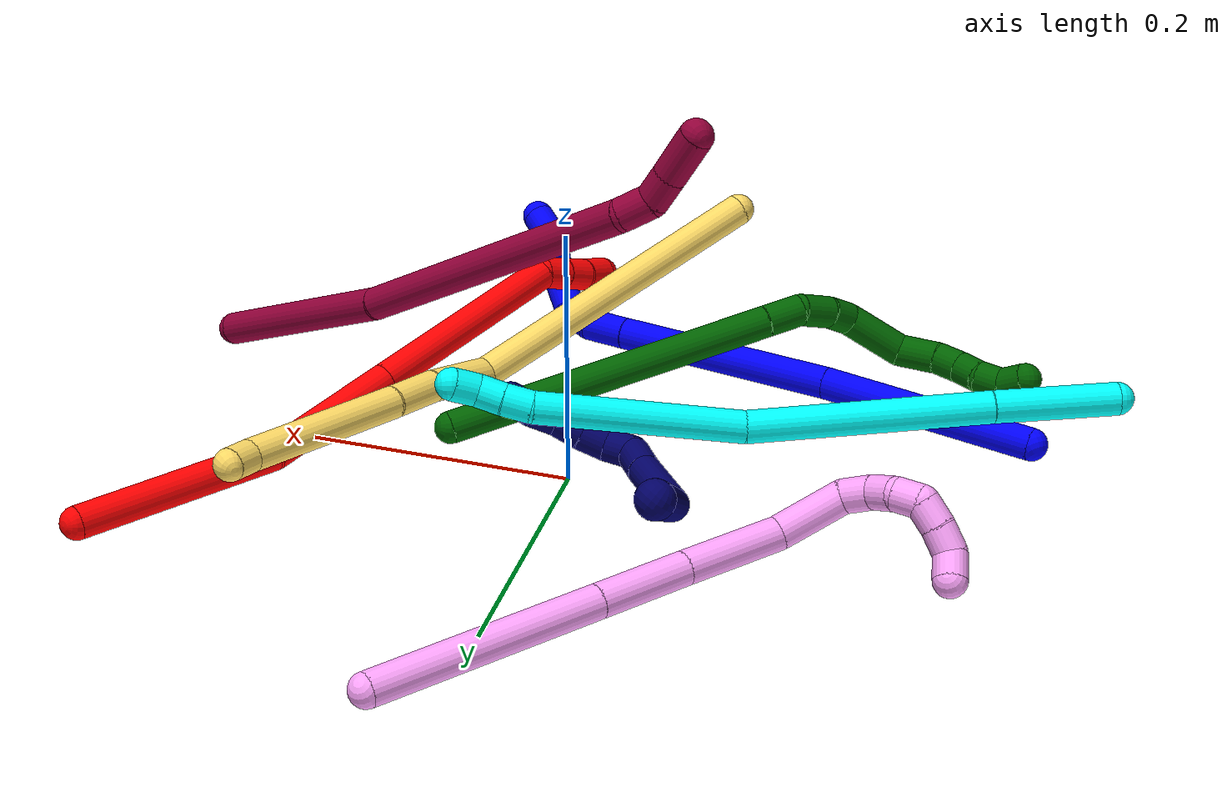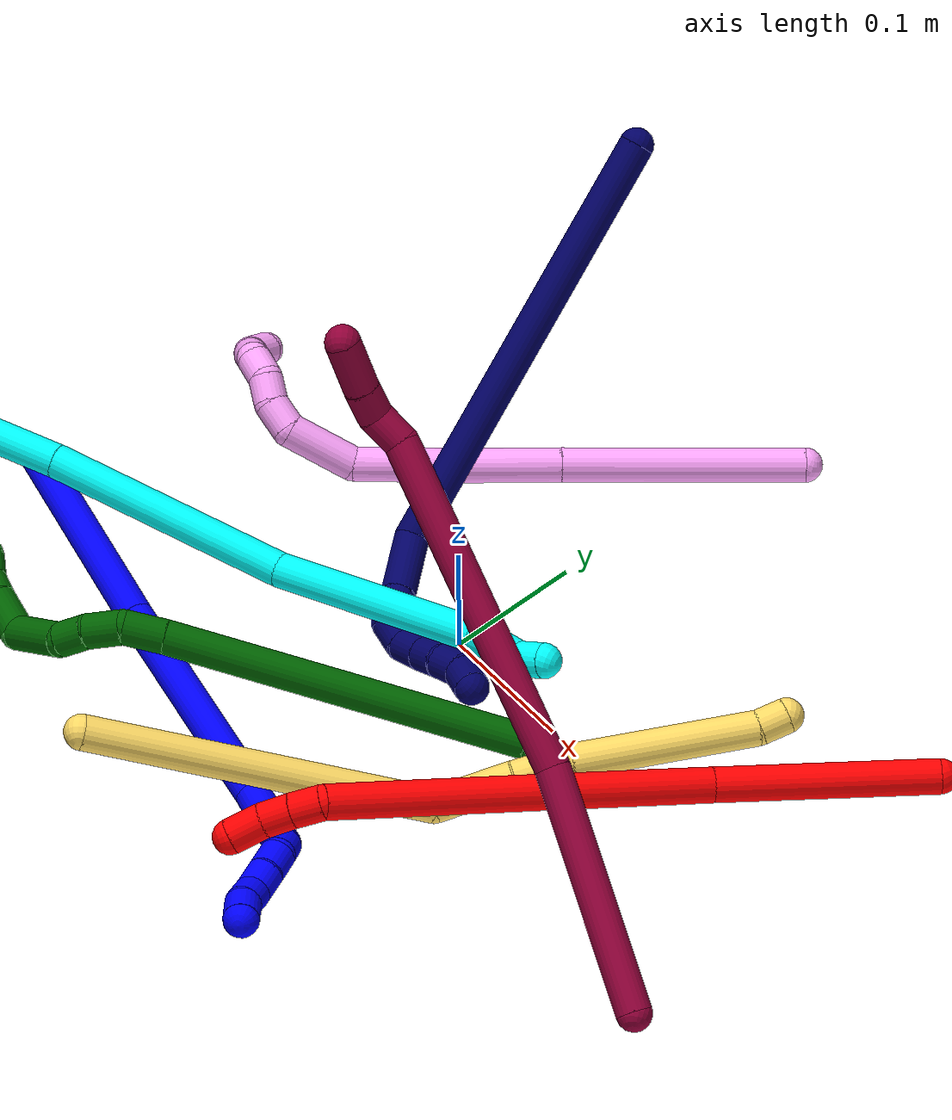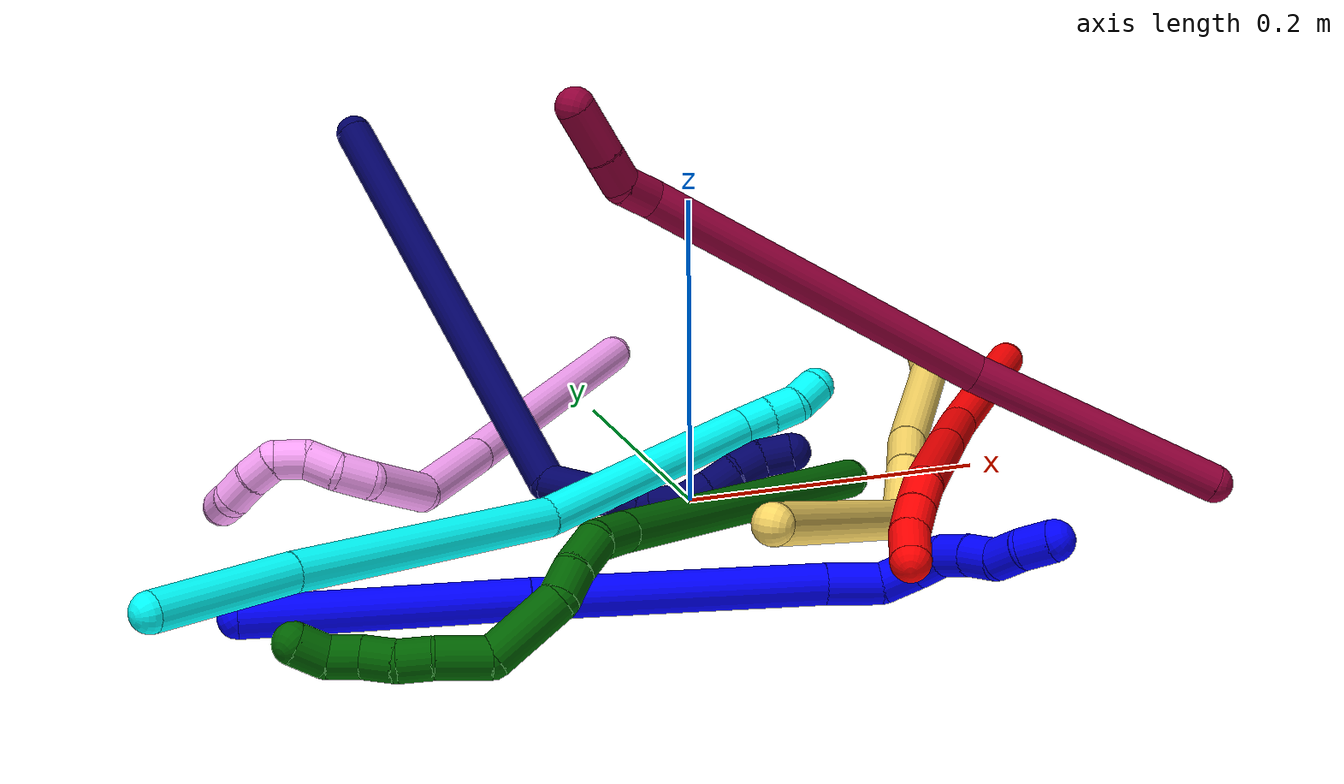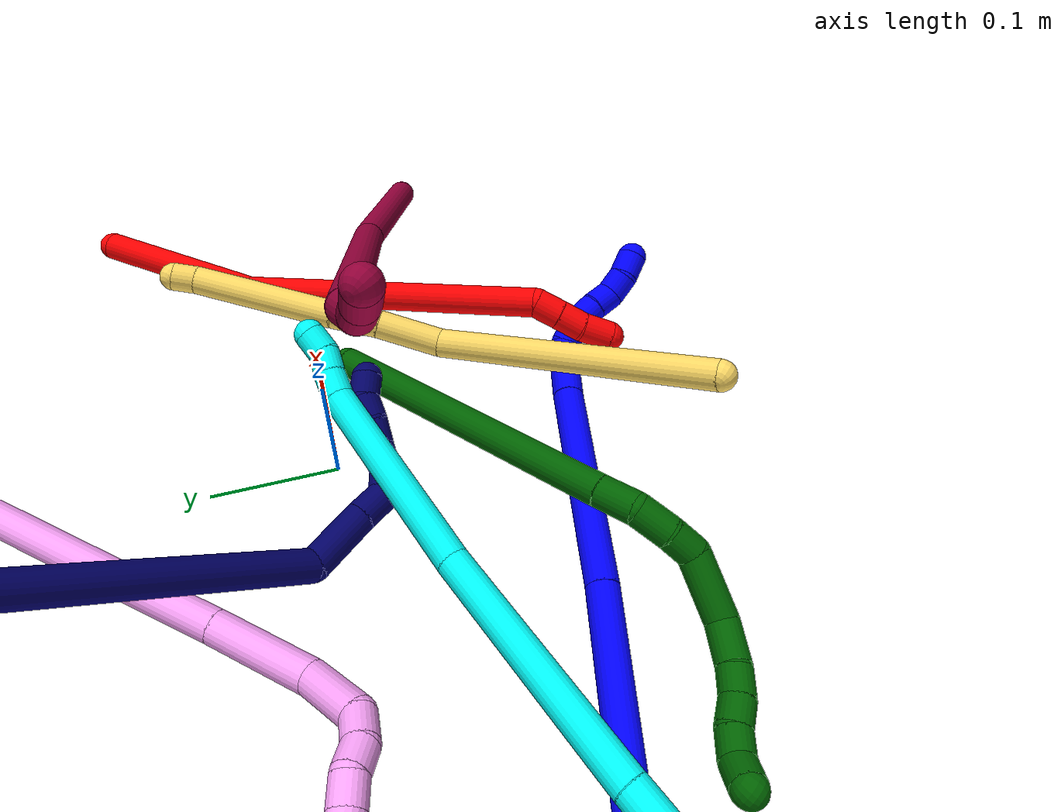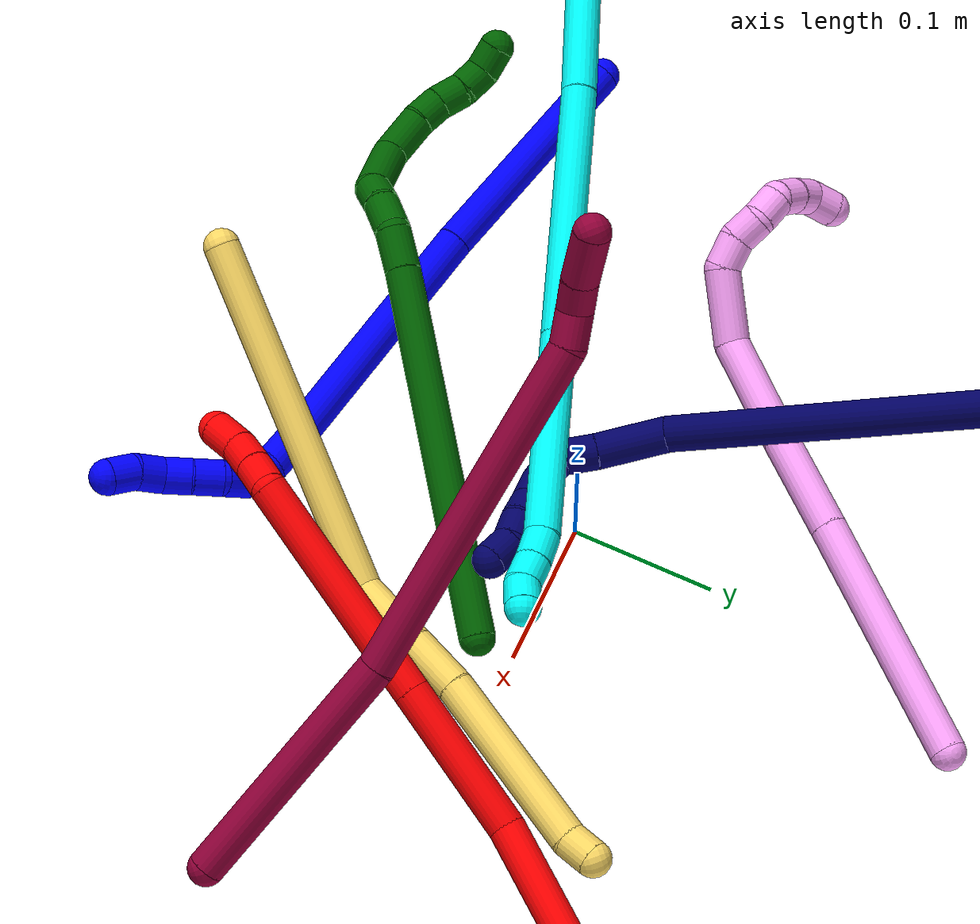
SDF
<sdf version="1.7">
 <world name="default">
  <plugin name="TubeGeneratorPlugin" filename="libtube_generator_plugin.so"/>
  <model name="photoneo_s_sensor">
   <static>1</static>
   <pose>0 0 2 1.57079 1.57079 3.14159</pose>
   <link name="link">
    <inertial><mass>0.1</mass></inertial>
    <sensor name="sensor" type="depth">
     <update_rate>30</update_rate>
     <camera>
      <horizontal_fov>1.22</horizontal_fov>
      <image><width>1920</width><height>1200</height><format>B8G8R8</format></image>
      <clip><near>0.1</near><far>4</far></clip>
      <depth_camera><output>points</output></depth_camera>
     </camera>
     <plugin name="camera_plugin" filename="libgazebo_ros_depth_camera.so">
      <baseline>0.2</baseline>
      <alwaysOn>1</alwaysOn>
      <updateRate>0.0</updateRate>
      <cameraName>camera_ir</cameraName>
      <imageTopicName>/camera/color/image_raw</imageTopicName>
      <cameraInfoTopicName>/camera/color/camera_info</cameraInfoTopicName>
      <depthImageTopicName>/camera/depth/image_raw</depthImageTopicName>
      <depthImageCameraInfoTopicName>/camera/depth/camera_info</depthImageCameraInfoTopicName>
      <pointCloudTopicName>/camera/depth/points</pointCloudTopicName>
      <frameName>fr_optical</frameName>
      <pointCloudCutoff>0.1</pointCloudCutoff>
      <pointCloudCutoffMax>2.0</pointCloudCutoffMax>
      <distortionK1>0</distortionK1>
      <distortionK2>0</distortionK2>
      <distortionK3>0</distortionK3>
      <distortionT1>0</distortionT1>
      <distortionT2>0</distortionT2>
      <CxPrime>0</CxPrime>
      <Cx>0</Cx>
      <Cy>0</Cy>
      <focalLength>0</focalLength>
      <hackBaseline>0</hackBaseline>
     </plugin>
    </sensor>
   </link>
  </model>
  <gravity>0 0 -9.8</gravity>
  <magnetic_field>6e-06 2.3e-05 -4.2e-05</magnetic_field>
  <atmosphere type="adiabatic"/>
  <physics name="default_physics" default="0" type="ode">
   <max_step_size>0.003</max_step_size>
   <real_time_factor>1</real_time_factor>
   <real_time_update_rate>1000</real_time_update_rate>
   <max_contacts>10000</max_contacts>
   <ode>
    <solver>
     <type>quick</type>
     <iters>100</iters>
     <sor>1.3</sor>
     <use_dynamic_moi_rescaling>0</use_dynamic_moi_rescaling>
    </solver>
    <constraints>
     <contact_max_correcting_vel>0</contact_max_correcting_vel>
     <contact_surface_layer>0.001</contact_surface_layer>
     <cfm>0</cfm>
     <erp>0.2</erp>
    </constraints>
   </ode>
  </physics>
  <scene><ambient>0.4 0.4 0.4 1</ambient><background>0.7 0.7 0.7 1</background><shadows>0</shadows></scene>
  <audio><device>default</device></audio>
  <spherical_coordinates>
   <surface_model>EARTH_WGS84</surface_model>
   <latitude_deg>0</latitude_deg>
   <longitude_deg>0</longitude_deg>
   <elevation>0</elevation>
   <heading_deg>0</heading_deg>
  </spherical_coordinates>
  <model name="bin">
   <static>1</static>
   <link name="bottom">
    <collision name="collision-bottom">
     <pose>0 0 -0.01 0 -0 0</pose>
     <geometry><box><size>0.8 0.6 0.02</size></box></geometry>
     <surface>
      <friction><ode><mu>100</mu><mu2>100</mu2></ode></friction>
      <contact><collide_bitmask>65535</collide_bitmask></contact>
     </surface>
    </collision>
   </link>
   <link name="west_wall">
    <collision name="collision-west_wall">
     <pose>-0.41 0 0.1 0 -0 0</pose>
     <geometry><box><size>0.02 0.6 0.2</size></box></geometry>
     <surface>
      <friction><ode><mu>100</mu><mu2>100</mu2></ode></friction>
      <contact><collide_bitmask>65535</collide_bitmask></contact>
     </surface>
    </collision>
   </link>
   <link name="east_wall">
    <collision name="collision-east_wall">
     <pose>0.41 0 0.1 0 -0 0</pose>
     <geometry><box><size>0.02 0.6 0.2</size></box></geometry>
     <surface>
      <friction><ode><mu>100</mu><mu2>100</mu2></ode></friction>
      <contact><collide_bitmask>65535</collide_bitmask></contact>
     </surface>
    </collision>
   </link>
   <link name="south_wall">
    <collision name="collision-south_wall">
     <pose>0 -0.31 0.1 0 -0 0</pose>
     <geometry><box><size>0.8 0.02 0.2</size></box></geometry>
     <surface>
      <friction><ode><mu>100</mu><mu2>100</mu2></ode></friction>
      <contact><collide_bitmask>65535</collide_bitmask></contact>
     </surface>
    </collision>
   </link>
   <link name="north_wall">
    <collision name="collision-north_wall">
     <pose>0 0.31 0.1 0 -0 0</pose>
     <geometry><box><size>0.8 0.02 0.2</size></box></geometry>
     <surface>
      <friction><ode><mu>100</mu><mu2>100</mu2></ode></friction>
      <contact><collide_bitmask>65535</collide_bitmask></contact>
     </surface>
    </collision>
   </link>
  </model>
  <model name="1">
   <static>0</static>
   <link name="1">
    <collision name="collision-cylinder-e_1_1_4">
     <pose>0.058591 0.015734 -0.058097 -2.87712 0.771937 -2.50891</pose>
     <geometry><cylinder><radius>0.0125</radius><length>0.167997</length></cylinder></geometry>
     <surface>
      <friction><ode><mu>1.16</mu><mu2>1.16</mu2><slip1>0</slip1><slip2>0</slip2></ode></friction>
      <contact><ode><kp>1e+06</kp><kd>1</kd><max_vel>0</max_vel><min_depth>0.001</min_depth></ode></contact>
     </surface>
    </collision>
    <visual name="visual-cylinder-e_1_1_4">
     <pose>0.058591 0.015734 -0.058097 -2.87712 0.771937 -2.50891</pose>
     <geometry><cylinder><radius>0.0125</radius><length>0.167997</length></cylinder></geometry>
     <material><ambient>0 0 1 1</ambient></material>
    </visual>
    <collision name="collision-cylinder-e_2_4_5">
     <pose>0.180741 0.047895 -0.173407 -2.86197 0.818168 -2.51384</pose>
     <geometry><cylinder><radius>0.0125</radius><length>0.174158</length></cylinder></geometry>
     <surface>
      <friction><ode><mu>1.16</mu><mu2>1.16</mu2><slip1>0</slip1><slip2>0</slip2></ode></friction>
      <contact><ode><kp>1e+06</kp><kd>1</kd><max_vel>0</max_vel><min_depth>0.001</min_depth></ode></contact>
     </surface>
    </collision>
    <visual name="visual-cylinder-e_2_4_5">
     <pose>0.180741 0.047895 -0.173407 -2.86197 0.818168 -2.51384</pose>
     <geometry><cylinder><radius>0.0125</radius><length>0.174158</length></cylinder></geometry>
     <material><ambient>0 0 1 1</ambient></material>
    </visual>
    <collision name="collision-cylinder-e_3_5_6">
     <pose>0.256263 0.068381 -0.241979 -2.79855 0.781269 -2.34523</pose>
     <geometry><cylinder><radius>0.0125</radius><length>0.03398</length></cylinder></geometry>
     <surface>
      <friction><ode><mu>1.16</mu><mu2>1.16</mu2><slip1>0</slip1><slip2>0</slip2></ode></friction>
      <contact><ode><kp>1e+06</kp><kd>1</kd><max_vel>0</max_vel><min_depth>0.001</min_depth></ode></contact>
     </surface>
    </collision>
    <visual name="visual-cylinder-e_3_5_6">
     <pose>0.256263 0.068381 -0.241979 -2.79855 0.781269 -2.34523</pose>
     <geometry><cylinder><radius>0.0125</radius><length>0.03398</length></cylinder></geometry>
     <material><ambient>0 0 1 1</ambient></material>
    </visual>
    <collision name="collision-cylinder-e_4_6_7">
     <pose>0.273156 0.071512 -0.263373 3.0495 0.454926 2.74858</pose>
     <geometry><cylinder><radius>0.0125</radius><length>0.022435</length></cylinder></geometry>
     <surface>
      <friction><ode><mu>1.16</mu><mu2>1.16</mu2><slip1>0</slip1><slip2>0</slip2></ode></friction>
      <contact><ode><kp>1e+06</kp><kd>1</kd><max_vel>0</max_vel><min_depth>0.001</min_depth></ode></contact>
     </surface>
    </collision>
    <visual name="visual-cylinder-e_4_6_7">
     <pose>0.273156 0.071512 -0.263373 3.0495 0.454926 2.74858</pose>
     <geometry><cylinder><radius>0.0125</radius><length>0.022435</length></cylinder></geometry>
     <material><ambient>0 0 1 1</ambient></material>
    </visual>
    <collision name="collision-cylinder-e_5_7_8">
     <pose>0.277556 0.070532 -0.283701 3.13638 -0.051387 -2.93948</pose>
     <geometry><cylinder><radius>0.0125</radius><length>0.020617</length></cylinder></geometry>
     <surface>
      <friction><ode><mu>1.16</mu><mu2>1.16</mu2><slip1>0</slip1><slip2>0</slip2></ode></friction>
      <contact><ode><kp>1e+06</kp><kd>1</kd><max_vel>0</max_vel><min_depth>0.001</min_depth></ode></contact>
     </surface>
    </collision>
    <visual name="visual-cylinder-e_5_7_8">
     <pose>0.277556 0.070532 -0.283701 3.13638 -0.051387 -2.93948</pose>
     <geometry><cylinder><radius>0.0125</radius><length>0.020617</length></cylinder></geometry>
     <material><ambient>0 0 1 1</ambient></material>
    </visual>
    <collision name="collision-cylinder-e_6_8_9">
     <pose>0.276018 0.074273 -0.303468 -2.76051 -0.09849 0.500337</pose>
     <geometry><cylinder><radius>0.0125</radius><length>0.020506</length></cylinder></geometry>
     <surface>
      <friction><ode><mu>1.16</mu><mu2>1.16</mu2><slip1>0</slip1><slip2>0</slip2></ode></friction>
      <contact><ode><kp>1e+06</kp><kd>1</kd><max_vel>0</max_vel><min_depth>0.001</min_depth></ode></contact>
     </surface>
    </collision>
    <visual name="visual-cylinder-e_6_8_9">
     <pose>0.276018 0.074273 -0.303468 -2.76051 -0.09849 0.500337</pose>
     <geometry><cylinder><radius>0.0125</radius><length>0.020506</length></cylinder></geometry>
     <material><ambient>0 0 1 1</ambient></material>
    </visual>
    <collision name="collision-cylinder-e_7_9_10">
     <pose>0.273885 0.082958 -0.321637 -2.62942 -0.112232 0.42268</pose>
     <geometry><cylinder><radius>0.0125</radius><length>0.020083</length></cylinder></geometry>
     <surface>
      <friction><ode><mu>1.16</mu><mu2>1.16</mu2><slip1>0</slip1><slip2>0</slip2></ode></friction>
      <contact><ode><kp>1e+06</kp><kd>1</kd><max_vel>0</max_vel><min_depth>0.001</min_depth></ode></contact>
     </surface>
    </collision>
    <visual name="visual-cylinder-e_7_9_10">
     <pose>0.273885 0.082958 -0.321637 -2.62942 -0.112232 0.42268</pose>
     <geometry><cylinder><radius>0.0125</radius><length>0.020083</length></cylinder></geometry>
     <material><ambient>0 0 1 1</ambient></material>
    </visual>
    <collision name="collision-cylinder-e_8_10_11">
     <pose>0.271443 0.088643 -0.340262 -3.06164 -0.131517 2.04995</pose>
     <geometry><cylinder><radius>0.0125</radius><length>0.020091</length></cylinder></geometry>
     <surface>
      <friction><ode><mu>1.16</mu><mu2>1.16</mu2><slip1>0</slip1><slip2>0</slip2></ode></friction>
      <contact><ode><kp>1e+06</kp><kd>1</kd><max_vel>0</max_vel><min_depth>0.001</min_depth></ode></contact>
     </surface>
    </collision>
    <visual name="visual-cylinder-e_8_10_11">
     <pose>0.271443 0.088643 -0.340262 -3.06164 -0.131517 2.04995</pose>
     <geometry><cylinder><radius>0.0125</radius><length>0.020091</length></cylinder></geometry>
     <material><ambient>0 0 1 1</ambient></material>
    </visual>
    <collision name="collision-cylinder-e_9_11_2">
     <pose>0.271717 0.090711 -0.360047 -3.01322 0.158725 -1.78218</pose>
     <geometry><cylinder><radius>0.0125</radius><length>0.020133</length></cylinder></geometry>
     <surface>
      <friction><ode><mu>1.16</mu><mu2>1.16</mu2><slip1>0</slip1><slip2>0</slip2></ode></friction>
      <contact><ode><kp>1e+06</kp><kd>1</kd><max_vel>0</max_vel><min_depth>0.001</min_depth></ode></contact>
     </surface>
    </collision>
    <visual name="visual-cylinder-e_9_11_2">
     <pose>0.271717 0.090711 -0.360047 -3.01322 0.158725 -1.78218</pose>
     <geometry><cylinder><radius>0.0125</radius><length>0.020133</length></cylinder></geometry>
     <material><ambient>0 0 1 1</ambient></material>
    </visual>
    <collision name="collision-sphere-2">
     <pose>0.273308 0.091984 -0.369905 0 -0 0</pose>
     <geometry><sphere><radius>0.0125</radius></sphere></geometry>
     <surface>
      <friction><ode><mu>1.16</mu><mu2>1.16</mu2><slip1>0</slip1><slip2>0</slip2></ode></friction>
      <contact><ode><kp>1e+06</kp><kd>1</kd><max_vel>0</max_vel><min_depth>0.001</min_depth></ode></contact>
     </surface>
    </collision>
    <visual name="visual-sphere-2">
     <pose>0.273308 0.091984 -0.369905 0 -0 0</pose>
     <geometry><sphere><radius>0.0125</radius></sphere></geometry>
     <material><ambient>0 0 1 1</ambient></material>
    </visual>
    <collision name="collision-sphere-11">
     <pose>0.270126 0.089439 -0.350188 0 -0 0</pose>
     <geometry><sphere><radius>0.0125</radius></sphere></geometry>
     <surface>
      <friction><ode><mu>1.16</mu><mu2>1.16</mu2><slip1>0</slip1><slip2>0</slip2></ode></friction>
      <contact><ode><kp>1e+06</kp><kd>1</kd><max_vel>0</max_vel><min_depth>0.001</min_depth></ode></contact>
     </surface>
    </collision>
    <visual name="visual-sphere-11">
     <pose>0.270126 0.089439 -0.350188 0 -0 0</pose>
     <geometry><sphere><radius>0.0125</radius></sphere></geometry>
     <material><ambient>0 0 1 1</ambient></material>
    </visual>
    <collision name="collision-sphere-10">
     <pose>0.27276 0.087848 -0.330335 0 -0 0</pose>
     <geometry><sphere><radius>0.0125</radius></sphere></geometry>
     <surface>
      <friction><ode><mu>1.16</mu><mu2>1.16</mu2><slip1>0</slip1><slip2>0</slip2></ode></friction>
      <contact><ode><kp>1e+06</kp><kd>1</kd><max_vel>0</max_vel><min_depth>0.001</min_depth></ode></contact>
     </surface>
    </collision>
    <visual name="visual-sphere-10">
     <pose>0.27276 0.087848 -0.330335 0 -0 0</pose>
     <geometry><sphere><radius>0.0125</radius></sphere></geometry>
     <material><ambient>0 0 1 1</ambient></material>
    </visual>
    <collision name="collision-sphere-9">
     <pose>0.27501 0.078068 -0.312939 0 -0 0</pose>
     <geometry><sphere><radius>0.0125</radius></sphere></geometry>
     <surface>
      <friction><ode><mu>1.16</mu><mu2>1.16</mu2><slip1>0</slip1><slip2>0</slip2></ode></friction>
      <contact><ode><kp>1e+06</kp><kd>1</kd><max_vel>0</max_vel><min_depth>0.001</min_depth></ode></contact>
     </surface>
    </collision>
    <visual name="visual-sphere-9">
     <pose>0.27501 0.078068 -0.312939 0 -0 0</pose>
     <geometry><sphere><radius>0.0125</radius></sphere></geometry>
     <material><ambient>0 0 1 1</ambient></material>
    </visual>
    <collision name="collision-sphere-4">
     <pose>0.117182 0.031467 -0.116195 0 -0 0</pose>
     <geometry><sphere><radius>0.0125</radius></sphere></geometry>
     <surface>
      <friction><ode><mu>1.16</mu><mu2>1.16</mu2><slip1>0</slip1><slip2>0</slip2></ode></friction>
      <contact><ode><kp>1e+06</kp><kd>1</kd><max_vel>0</max_vel><min_depth>0.001</min_depth></ode></contact>
     </surface>
    </collision>
    <visual name="visual-sphere-4">
     <pose>0.117182 0.031467 -0.116195 0 -0 0</pose>
     <geometry><sphere><radius>0.0125</radius></sphere></geometry>
     <material><ambient>0 0 1 1</ambient></material>
    </visual>
    <collision name="collision-sphere-1">
     <geometry><sphere><radius>0.0125</radius></sphere></geometry>
     <surface>
      <friction><ode><mu>1.16</mu><mu2>1.16</mu2><slip1>0</slip1><slip2>0</slip2></ode></friction>
      <contact><ode><kp>1e+06</kp><kd>1</kd><max_vel>0</max_vel><min_depth>0.001</min_depth></ode></contact>
     </surface>
    </collision>
    <visual name="visual-sphere-1">
     <geometry><sphere><radius>0.0125</radius></sphere></geometry>
     <material><ambient>0 0 1 1</ambient></material>
    </visual>
    <collision name="collision-sphere-8">
     <pose>0.277026 0.070478 -0.293996 0 -0 0</pose>
     <geometry><sphere><radius>0.0125</radius></sphere></geometry>
     <surface>
      <friction><ode><mu>1.16</mu><mu2>1.16</mu2><slip1>0</slip1><slip2>0</slip2></ode></friction>
      <contact><ode><kp>1e+06</kp><kd>1</kd><max_vel>0</max_vel><min_depth>0.001</min_depth></ode></contact>
     </surface>
    </collision>
    <visual name="visual-sphere-8">
     <pose>0.277026 0.070478 -0.293996 0 -0 0</pose>
     <geometry><sphere><radius>0.0125</radius></sphere></geometry>
     <material><ambient>0 0 1 1</ambient></material>
    </visual>
    <collision name="collision-sphere-5">
     <pose>0.244299 0.064324 -0.230618 0 -0 0</pose>
     <geometry><sphere><radius>0.0125</radius></sphere></geometry>
     <surface>
      <friction><ode><mu>1.16</mu><mu2>1.16</mu2><slip1>0</slip1><slip2>0</slip2></ode></friction>
      <contact><ode><kp>1e+06</kp><kd>1</kd><max_vel>0</max_vel><min_depth>0.001</min_depth></ode></contact>
     </surface>
    </collision>
    <visual name="visual-sphere-5">
     <pose>0.244299 0.064324 -0.230618 0 -0 0</pose>
     <geometry><sphere><radius>0.0125</radius></sphere></geometry>
     <material><ambient>0 0 1 1</ambient></material>
    </visual>
    <collision name="collision-sphere-6">
     <pose>0.268227 0.072439 -0.253339 0 -0 0</pose>
     <geometry><sphere><radius>0.0125</radius></sphere></geometry>
     <surface>
      <friction><ode><mu>1.16</mu><mu2>1.16</mu2><slip1>0</slip1><slip2>0</slip2></ode></friction>
      <contact><ode><kp>1e+06</kp><kd>1</kd><max_vel>0</max_vel><min_depth>0.001</min_depth></ode></contact>
     </surface>
    </collision>
    <visual name="visual-sphere-6">
     <pose>0.268227 0.072439 -0.253339 0 -0 0</pose>
     <geometry><sphere><radius>0.0125</radius></sphere></geometry>
     <material><ambient>0 0 1 1</ambient></material>
    </visual>
    <collision name="collision-sphere-7">
     <pose>0.278085 0.070585 -0.273407 0 -0 0</pose>
     <geometry><sphere><radius>0.0125</radius></sphere></geometry>
     <surface>
      <friction><ode><mu>1.16</mu><mu2>1.16</mu2><slip1>0</slip1><slip2>0</slip2></ode></friction>
      <contact><ode><kp>1e+06</kp><kd>1</kd><max_vel>0</max_vel><min_depth>0.001</min_depth></ode></contact>
     </surface>
    </collision>
    <visual name="visual-sphere-7">
     <pose>0.278085 0.070585 -0.273407 0 -0 0</pose>
     <geometry><sphere><radius>0.0125</radius></sphere></geometry>
     <material><ambient>0 0 1 1</ambient></material>
    </visual>
    <inertial>
     <pose>0.167927 0.046326 -0.173416 0 -0 0</pose>
     <mass>0.5</mass>
     <inertia>
      <ixx>-0.000812</ixx>
      <ixy>0</ixy>
      <ixz>0</ixz>
      <iyy>0.000419</iyy>
      <iyz>0</iyz>
      <izz>-0.000801</izz>
     </inertia>
    </inertial>
   </link>
   <pose>-0.320886 -0.125487 0.011495 -2.18358 0.311789 0.509385</pose>
  </model>
  <model name="2">
   <static>0</static>
   <link name="2">
    <collision name="collision-cylinder-e_1_1_4">
     <pose>-0.025852 -0.006626 -0.073571 3.05177 -0.336645 -2.62448</pose>
     <geometry><cylinder><radius>0.0125</radius><length>0.156524</length></cylinder></geometry>
     <surface>
      <friction><ode><mu>1.16</mu><mu2>1.16</mu2><slip1>0</slip1><slip2>0</slip2></ode></friction>
      <contact><ode><kp>1e+06</kp><kd>1</kd><max_vel>0</max_vel><min_depth>0.001</min_depth></ode></contact>
     </surface>
    </collision>
    <visual name="visual-cylinder-e_1_1_4">
     <pose>-0.025852 -0.006626 -0.073571 3.05177 -0.336645 -2.62448</pose>
     <geometry><cylinder><radius>0.0125</radius><length>0.156524</length></cylinder></geometry>
     <material><ambient>1 0 0 1</ambient></material>
    </visual>
    <collision name="collision-cylinder-e_2_4_5">
     <pose>-0.06712 -0.030538 -0.196327 2.80364 -0.287523 -1.40728</pose>
     <geometry><cylinder><radius>0.0125</radius><length>0.108731</length></cylinder></geometry>
     <surface>
      <friction><ode><mu>1.16</mu><mu2>1.16</mu2><slip1>0</slip1><slip2>0</slip2></ode></friction>
      <contact><ode><kp>1e+06</kp><kd>1</kd><max_vel>0</max_vel><min_depth>0.001</min_depth></ode></contact>
     </surface>
    </collision>
    <visual name="visual-cylinder-e_2_4_5">
     <pose>-0.06712 -0.030538 -0.196327 2.80364 -0.287523 -1.40728</pose>
     <geometry><cylinder><radius>0.0125</radius><length>0.108731</length></cylinder></geometry>
     <material><ambient>1 0 0 1</ambient></material>
    </visual>
    <collision name="collision-cylinder-e_3_5_6">
     <pose>-0.105866 -0.074085 -0.320647 2.80533 -0.285122 -1.40394</pose>
     <geometry><cylinder><radius>0.0125</radius><length>0.165882</length></cylinder></geometry>
     <surface>
      <friction><ode><mu>1.16</mu><mu2>1.16</mu2><slip1>0</slip1><slip2>0</slip2></ode></friction>
      <contact><ode><kp>1e+06</kp><kd>1</kd><max_vel>0</max_vel><min_depth>0.001</min_depth></ode></contact>
     </surface>
    </collision>
    <visual name="visual-cylinder-e_3_5_6">
     <pose>-0.105866 -0.074085 -0.320647 2.80533 -0.285122 -1.40394</pose>
     <geometry><cylinder><radius>0.0125</radius><length>0.165882</length></cylinder></geometry>
     <material><ambient>1 0 0 1</ambient></material>
    </visual>
    <collision name="collision-cylinder-e_4_6_7">
     <pose>-0.130734 -0.098406 -0.40652 -2.96279 -0.140063 1.32799</pose>
     <geometry><cylinder><radius>0.0125</radius><length>0.022039</length></cylinder></geometry>
     <surface>
      <friction><ode><mu>1.16</mu><mu2>1.16</mu2><slip1>0</slip1><slip2>0</slip2></ode></friction>
      <contact><ode><kp>1e+06</kp><kd>1</kd><max_vel>0</max_vel><min_depth>0.001</min_depth></ode></contact>
     </surface>
    </collision>
    <visual name="visual-cylinder-e_4_6_7">
     <pose>-0.130734 -0.098406 -0.40652 -2.96279 -0.140063 1.32799</pose>
     <geometry><cylinder><radius>0.0125</radius><length>0.022039</length></cylinder></geometry>
     <material><ambient>1 0 0 1</ambient></material>
    </visual>
    <collision name="collision-cylinder-e_5_7_8">
     <pose>-0.133255 -0.094284 -0.427915 -2.93965 -0.090068 0.837036</pose>
     <geometry><cylinder><radius>0.0125</radius><length>0.021847</length></cylinder></geometry>
     <surface>
      <friction><ode><mu>1.16</mu><mu2>1.16</mu2><slip1>0</slip1><slip2>0</slip2></ode></friction>
      <contact><ode><kp>1e+06</kp><kd>1</kd><max_vel>0</max_vel><min_depth>0.001</min_depth></ode></contact>
     </surface>
    </collision>
    <visual name="visual-cylinder-e_5_7_8">
     <pose>-0.133255 -0.094284 -0.427915 -2.93965 -0.090068 0.837036</pose>
     <geometry><cylinder><radius>0.0125</radius><length>0.021847</length></cylinder></geometry>
     <material><ambient>1 0 0 1</ambient></material>
    </visual>
    <collision name="collision-cylinder-e_6_8_2">
     <pose>-0.133421 -0.091126 -0.450997 -3.06321 0.065439 -1.39115</pose>
     <geometry><cylinder><radius>0.0125</radius><length>0.024977</length></cylinder></geometry>
     <surface>
      <friction><ode><mu>1.16</mu><mu2>1.16</mu2><slip1>0</slip1><slip2>0</slip2></ode></friction>
      <contact><ode><kp>1e+06</kp><kd>1</kd><max_vel>0</max_vel><min_depth>0.001</min_depth></ode></contact>
     </surface>
    </collision>
    <visual name="visual-cylinder-e_6_8_2">
     <pose>-0.133421 -0.091126 -0.450997 -3.06321 0.065439 -1.39115</pose>
     <geometry><cylinder><radius>0.0125</radius><length>0.024977</length></cylinder></geometry>
     <material><ambient>1 0 0 1</ambient></material>
    </visual>
    <collision name="collision-sphere-2">
     <pose>-0.132604 -0.09015 -0.463421 0 -0 0</pose>
     <geometry><sphere><radius>0.0125</radius></sphere></geometry>
     <surface>
      <friction><ode><mu>1.16</mu><mu2>1.16</mu2><slip1>0</slip1><slip2>0</slip2></ode></friction>
      <contact><ode><kp>1e+06</kp><kd>1</kd><max_vel>0</max_vel><min_depth>0.001</min_depth></ode></contact>
     </surface>
    </collision>
    <visual name="visual-sphere-2">
     <pose>-0.132604 -0.09015 -0.463421 0 -0 0</pose>
     <geometry><sphere><radius>0.0125</radius></sphere></geometry>
     <material><ambient>1 0 0 1</ambient></material>
    </visual>
    <collision name="collision-sphere-4">
     <pose>-0.051703 -0.013253 -0.147143 0 -0 0</pose>
     <geometry><sphere><radius>0.0125</radius></sphere></geometry>
     <surface>
      <friction><ode><mu>1.16</mu><mu2>1.16</mu2><slip1>0</slip1><slip2>0</slip2></ode></friction>
      <contact><ode><kp>1e+06</kp><kd>1</kd><max_vel>0</max_vel><min_depth>0.001</min_depth></ode></contact>
     </surface>
    </collision>
    <visual name="visual-sphere-4">
     <pose>-0.051703 -0.013253 -0.147143 0 -0 0</pose>
     <geometry><sphere><radius>0.0125</radius></sphere></geometry>
     <material><ambient>1 0 0 1</ambient></material>
    </visual>
    <collision name="collision-sphere-1">
     <geometry><sphere><radius>0.0125</radius></sphere></geometry>
     <surface>
      <friction><ode><mu>1.16</mu><mu2>1.16</mu2><slip1>0</slip1><slip2>0</slip2></ode></friction>
      <contact><ode><kp>1e+06</kp><kd>1</kd><max_vel>0</max_vel><min_depth>0.001</min_depth></ode></contact>
     </surface>
    </collision>
    <visual name="visual-sphere-1">
     <geometry><sphere><radius>0.0125</radius></sphere></geometry>
     <material><ambient>1 0 0 1</ambient></material>
    </visual>
    <collision name="collision-sphere-8">
     <pose>-0.134237 -0.092102 -0.438574 0 -0 0</pose>
     <geometry><sphere><radius>0.0125</radius></sphere></geometry>
     <surface>
      <friction><ode><mu>1.16</mu><mu2>1.16</mu2><slip1>0</slip1><slip2>0</slip2></ode></friction>
      <contact><ode><kp>1e+06</kp><kd>1</kd><max_vel>0</max_vel><min_depth>0.001</min_depth></ode></contact>
     </surface>
    </collision>
    <visual name="visual-sphere-8">
     <pose>-0.134237 -0.092102 -0.438574 0 -0 0</pose>
     <geometry><sphere><radius>0.0125</radius></sphere></geometry>
     <material><ambient>1 0 0 1</ambient></material>
    </visual>
    <collision name="collision-sphere-5">
     <pose>-0.082537 -0.047823 -0.245512 0 -0 0</pose>
     <geometry><sphere><radius>0.0125</radius></sphere></geometry>
     <surface>
      <friction><ode><mu>1.16</mu><mu2>1.16</mu2><slip1>0</slip1><slip2>0</slip2></ode></friction>
      <contact><ode><kp>1e+06</kp><kd>1</kd><max_vel>0</max_vel><min_depth>0.001</min_depth></ode></contact>
     </surface>
    </collision>
    <visual name="visual-sphere-5">
     <pose>-0.082537 -0.047823 -0.245512 0 -0 0</pose>
     <geometry><sphere><radius>0.0125</radius></sphere></geometry>
     <material><ambient>1 0 0 1</ambient></material>
    </visual>
    <collision name="collision-sphere-6">
     <pose>-0.129195 -0.100347 -0.395782 0 -0 0</pose>
     <geometry><sphere><radius>0.0125</radius></sphere></geometry>
     <surface>
      <friction><ode><mu>1.16</mu><mu2>1.16</mu2><slip1>0</slip1><slip2>0</slip2></ode></friction>
      <contact><ode><kp>1e+06</kp><kd>1</kd><max_vel>0</max_vel><min_depth>0.001</min_depth></ode></contact>
     </surface>
    </collision>
    <visual name="visual-sphere-6">
     <pose>-0.129195 -0.100347 -0.395782 0 -0 0</pose>
     <geometry><sphere><radius>0.0125</radius></sphere></geometry>
     <material><ambient>1 0 0 1</ambient></material>
    </visual>
    <collision name="collision-sphere-7">
     <pose>-0.132272 -0.096466 -0.417257 0 -0 0</pose>
     <geometry><sphere><radius>0.0125</radius></sphere></geometry>
     <surface>
      <friction><ode><mu>1.16</mu><mu2>1.16</mu2><slip1>0</slip1><slip2>0</slip2></ode></friction>
      <contact><ode><kp>1e+06</kp><kd>1</kd><max_vel>0</max_vel><min_depth>0.001</min_depth></ode></contact>
     </surface>
    </collision>
    <visual name="visual-sphere-7">
     <pose>-0.132272 -0.096466 -0.417257 0 -0 0</pose>
     <geometry><sphere><radius>0.0125</radius></sphere></geometry>
     <material><ambient>1 0 0 1</ambient></material>
    </visual>
    <inertial>
     <pose>-0.076061 -0.046303 -0.231249 0 -0 0</pose>
     <mass>0.5</mass>
     <inertia>
      <ixx>-0.000819</ixx>
      <ixy>0</ixy>
      <ixz>0</ixz>
      <iyy>-0.000377</iyy>
      <iyz>0</iyz>
      <izz>0.000397</izz>
     </inertia>
    </inertial>
   </link>
   <pose>0.308834 0.171238 0.012985 -1.30212 0.455526 -0.282962</pose>
  </model>
  <model name="3">
   <static>0</static>
   <link name="3">
    <collision name="collision-cylinder-e_1_1_4">
     <pose>0.0008 -0.000142 -0.047157 3.13858 0.016962 2.79062</pose>
     <geometry><cylinder><radius>0.0125</radius><length>0.094327</length></cylinder></geometry>
     <surface>
      <friction><ode><mu>1.16</mu><mu2>1.16</mu2><slip1>0</slip1><slip2>0</slip2></ode></friction>
      <contact><ode><kp>1e+06</kp><kd>1</kd><max_vel>0</max_vel><min_depth>0.001</min_depth></ode></contact>
     </surface>
    </collision>
    <visual name="visual-cylinder-e_1_1_4">
     <pose>0.0008 -0.000142 -0.047157 3.13858 0.016962 2.79062</pose>
     <geometry><cylinder><radius>0.0125</radius><length>0.094327</length></cylinder></geometry>
     <material><ambient>0.003922 1 0.996078 1</ambient></material>
    </visual>
    <collision name="collision-cylinder-e_2_4_5">
     <pose>0.007812 -0.002548 -0.186418 3.11701 0.067324 2.44171</pose>
     <geometry><cylinder><radius>0.0125</radius><length>0.184684</length></cylinder></geometry>
     <surface>
      <friction><ode><mu>1.16</mu><mu2>1.16</mu2><slip1>0</slip1><slip2>0</slip2></ode></friction>
      <contact><ode><kp>1e+06</kp><kd>1</kd><max_vel>0</max_vel><min_depth>0.001</min_depth></ode></contact>
     </surface>
    </collision>
    <visual name="visual-cylinder-e_2_4_5">
     <pose>0.007812 -0.002548 -0.186418 3.11701 0.067324 2.44171</pose>
     <geometry><cylinder><radius>0.0125</radius><length>0.184684</length></cylinder></geometry>
     <material><ambient>0.003922 1 0.996078 1</ambient></material>
    </visual>
    <collision name="collision-cylinder-e_3_5_6">
     <pose>0.012453 0.007952 -0.356887 -2.98013 -0.019787 0.243368</pose>
     <geometry><cylinder><radius>0.0125</radius><length>0.158824</length></cylinder></geometry>
     <surface>
      <friction><ode><mu>1.16</mu><mu2>1.16</mu2><slip1>0</slip1><slip2>0</slip2></ode></friction>
      <contact><ode><kp>1e+06</kp><kd>1</kd><max_vel>0</max_vel><min_depth>0.001</min_depth></ode></contact>
     </surface>
    </collision>
    <visual name="visual-cylinder-e_3_5_6">
     <pose>0.012453 0.007952 -0.356887 -2.98013 -0.019787 0.243368</pose>
     <geometry><cylinder><radius>0.0125</radius><length>0.158824</length></cylinder></geometry>
     <material><ambient>0.003922 1 0.996078 1</ambient></material>
    </visual>
    <collision name="collision-cylinder-e_4_6_7">
     <pose>0.012366 0.024098 -0.445477 -2.82217 0.136889 -0.804699</pose>
     <geometry><cylinder><radius>0.0125</radius><length>0.021746</length></cylinder></geometry>
     <surface>
      <friction><ode><mu>1.16</mu><mu2>1.16</mu2><slip1>0</slip1><slip2>0</slip2></ode></friction>
      <contact><ode><kp>1e+06</kp><kd>1</kd><max_vel>0</max_vel><min_depth>0.001</min_depth></ode></contact>
     </surface>
    </collision>
    <visual name="visual-cylinder-e_4_6_7">
     <pose>0.012366 0.024098 -0.445477 -2.82217 0.136889 -0.804699</pose>
     <geometry><cylinder><radius>0.0125</radius><length>0.021746</length></cylinder></geometry>
     <material><ambient>0.003922 1 0.996078 1</ambient></material>
    </visual>
    <collision name="collision-cylinder-e_5_7_8">
     <pose>0.015818 0.031242 -0.464949 -2.7552 0.194783 -0.926327</pose>
     <geometry><cylinder><radius>0.0125</radius><length>0.020347</length></cylinder></geometry>
     <surface>
      <friction><ode><mu>1.16</mu><mu2>1.16</mu2><slip1>0</slip1><slip2>0</slip2></ode></friction>
      <contact><ode><kp>1e+06</kp><kd>1</kd><max_vel>0</max_vel><min_depth>0.001</min_depth></ode></contact>
     </surface>
    </collision>
    <visual name="visual-cylinder-e_5_7_8">
     <pose>0.015818 0.031242 -0.464949 -2.7552 0.194783 -0.926327</pose>
     <geometry><cylinder><radius>0.0125</radius><length>0.020347</length></cylinder></geometry>
     <material><ambient>0.003922 1 0.996078 1</ambient></material>
    </visual>
    <collision name="collision-cylinder-e_6_8_2">
     <pose>0.015756 0.03813 -0.483511 -2.81775 -0.203815 1.11867</pose>
     <geometry><cylinder><radius>0.0125</radius><length>0.020072</length></cylinder></geometry>
     <surface>
      <friction><ode><mu>1.16</mu><mu2>1.16</mu2><slip1>0</slip1><slip2>0</slip2></ode></friction>
      <contact><ode><kp>1e+06</kp><kd>1</kd><max_vel>0</max_vel><min_depth>0.001</min_depth></ode></contact>
     </surface>
    </collision>
    <visual name="visual-cylinder-e_6_8_2">
     <pose>0.015756 0.03813 -0.483511 -2.81775 -0.203815 1.11867</pose>
     <geometry><cylinder><radius>0.0125</radius><length>0.020072</length></cylinder></geometry>
     <material><ambient>0.003922 1 0.996078 1</ambient></material>
    </visual>
    <collision name="collision-sphere-2">
     <pose>0.013725 0.041258 -0.492829 0 -0 0</pose>
     <geometry><sphere><radius>0.0125</radius></sphere></geometry>
     <surface>
      <friction><ode><mu>1.16</mu><mu2>1.16</mu2><slip1>0</slip1><slip2>0</slip2></ode></friction>
      <contact><ode><kp>1e+06</kp><kd>1</kd><max_vel>0</max_vel><min_depth>0.001</min_depth></ode></contact>
     </surface>
    </collision>
    <visual name="visual-sphere-2">
     <pose>0.013725 0.041258 -0.492829 0 -0 0</pose>
     <geometry><sphere><radius>0.0125</radius></sphere></geometry>
     <material><ambient>0.003922 1 0.996078 1</ambient></material>
    </visual>
    <collision name="collision-sphere-4">
     <pose>0.0016 -0.000284 -0.094313 0 -0 0</pose>
     <geometry><sphere><radius>0.0125</radius></sphere></geometry>
     <surface>
      <friction><ode><mu>1.16</mu><mu2>1.16</mu2><slip1>0</slip1><slip2>0</slip2></ode></friction>
      <contact><ode><kp>1e+06</kp><kd>1</kd><max_vel>0</max_vel><min_depth>0.001</min_depth></ode></contact>
     </surface>
    </collision>
    <visual name="visual-sphere-4">
     <pose>0.0016 -0.000284 -0.094313 0 -0 0</pose>
     <geometry><sphere><radius>0.0125</radius></sphere></geometry>
     <material><ambient>0.003922 1 0.996078 1</ambient></material>
    </visual>
    <collision name="collision-sphere-1">
     <geometry><sphere><radius>0.0125</radius></sphere></geometry>
     <surface>
      <friction><ode><mu>1.16</mu><mu2>1.16</mu2><slip1>0</slip1><slip2>0</slip2></ode></friction>
      <contact><ode><kp>1e+06</kp><kd>1</kd><max_vel>0</max_vel><min_depth>0.001</min_depth></ode></contact>
     </surface>
    </collision>
    <visual name="visual-sphere-1">
     <geometry><sphere><radius>0.0125</radius></sphere></geometry>
     <material><ambient>0.003922 1 0.996078 1</ambient></material>
    </visual>
    <collision name="collision-sphere-8">
     <pose>0.017788 0.035003 -0.474194 0 -0 0</pose>
     <geometry><sphere><radius>0.0125</radius></sphere></geometry>
     <surface>
      <friction><ode><mu>1.16</mu><mu2>1.16</mu2><slip1>0</slip1><slip2>0</slip2></ode></friction>
      <contact><ode><kp>1e+06</kp><kd>1</kd><max_vel>0</max_vel><min_depth>0.001</min_depth></ode></contact>
     </surface>
    </collision>
    <visual name="visual-sphere-8">
     <pose>0.017788 0.035003 -0.474194 0 -0 0</pose>
     <geometry><sphere><radius>0.0125</radius></sphere></geometry>
     <material><ambient>0.003922 1 0.996078 1</ambient></material>
    </visual>
    <collision name="collision-sphere-5">
     <pose>0.014024 -0.004812 -0.278523 0 -0 0</pose>
     <geometry><sphere><radius>0.0125</radius></sphere></geometry>
     <surface>
      <friction><ode><mu>1.16</mu><mu2>1.16</mu2><slip1>0</slip1><slip2>0</slip2></ode></friction>
      <contact><ode><kp>1e+06</kp><kd>1</kd><max_vel>0</max_vel><min_depth>0.001</min_depth></ode></contact>
     </surface>
    </collision>
    <visual name="visual-sphere-5">
     <pose>0.014024 -0.004812 -0.278523 0 -0 0</pose>
     <geometry><sphere><radius>0.0125</radius></sphere></geometry>
     <material><ambient>0.003922 1 0.996078 1</ambient></material>
    </visual>
    <collision name="collision-sphere-6">
     <pose>0.010882 0.020715 -0.43525 0 -0 0</pose>
     <geometry><sphere><radius>0.0125</radius></sphere></geometry>
     <surface>
      <friction><ode><mu>1.16</mu><mu2>1.16</mu2><slip1>0</slip1><slip2>0</slip2></ode></friction>
      <contact><ode><kp>1e+06</kp><kd>1</kd><max_vel>0</max_vel><min_depth>0.001</min_depth></ode></contact>
     </surface>
    </collision>
    <visual name="visual-sphere-6">
     <pose>0.010882 0.020715 -0.43525 0 -0 0</pose>
     <geometry><sphere><radius>0.0125</radius></sphere></geometry>
     <material><ambient>0.003922 1 0.996078 1</ambient></material>
    </visual>
    <collision name="collision-sphere-7">
     <pose>0.013849 0.02748 -0.455704 0 -0 0</pose>
     <geometry><sphere><radius>0.0125</radius></sphere></geometry>
     <surface>
      <friction><ode><mu>1.16</mu><mu2>1.16</mu2><slip1>0</slip1><slip2>0</slip2></ode></friction>
      <contact><ode><kp>1e+06</kp><kd>1</kd><max_vel>0</max_vel><min_depth>0.001</min_depth></ode></contact>
     </surface>
    </collision>
    <visual name="visual-sphere-7">
     <pose>0.013849 0.02748 -0.455704 0 -0 0</pose>
     <geometry><sphere><radius>0.0125</radius></sphere></geometry>
     <material><ambient>0.003922 1 0.996078 1</ambient></material>
    </visual>
    <inertial>
     <pose>0.008806 0.005408 -0.248823 0 -0 0</pose>
     <mass>0.5</mass>
     <inertia>
      <ixx>0.000307</ixx>
      <ixy>0</ixy>
      <ixz>0</ixz>
      <iyy>0.0006</iyy>
      <iyz>0</iyz>
      <izz>-0.000112</izz>
     </inertia>
    </inertial>
   </link>
   <pose>-0.376922 -0.165225 0.037869 1.56403 0.411958 -1.16963</pose>
  </model>
  <model name="4">
   <static>0</static>
   <link name="4">
    <collision name="collision-cylinder-e_1_1_4">
     <pose>-0.053124 -0.054586 0.042837 0.905416 -0.653422 -0.326699</pose>
     <geometry><cylinder><radius>0.0125</radius><length>0.174777</length></cylinder></geometry>
     <surface>
      <friction><ode><mu>1.16</mu><mu2>1.16</mu2><slip1>0</slip1><slip2>0</slip2></ode></friction>
      <contact><ode><kp>1e+06</kp><kd>1</kd><max_vel>0</max_vel><min_depth>0.001</min_depth></ode></contact>
     </surface>
    </collision>
    <visual name="visual-cylinder-e_1_1_4">
     <pose>-0.053124 -0.054586 0.042837 0.905416 -0.653422 -0.326699</pose>
     <geometry><cylinder><radius>0.0125</radius><length>0.174777</length></cylinder></geometry>
     <material><ambient>1 0.65098 0.996078 1</ambient></material>
    </visual>
    <collision name="collision-cylinder-e_2_4_5">
     <pose>-0.127848 -0.131004 0.103231 0.893513 -0.656782 -0.323605</pose>
     <geometry><cylinder><radius>0.0125</radius><length>0.070752</length></cylinder></geometry>
     <surface>
      <friction><ode><mu>1.16</mu><mu2>1.16</mu2><slip1>0</slip1><slip2>0</slip2></ode></friction>
      <contact><ode><kp>1e+06</kp><kd>1</kd><max_vel>0</max_vel><min_depth>0.001</min_depth></ode></contact>
     </surface>
    </collision>
    <visual name="visual-cylinder-e_2_4_5">
     <pose>-0.127848 -0.131004 0.103231 0.893513 -0.656782 -0.323605</pose>
     <geometry><cylinder><radius>0.0125</radius><length>0.070752</length></cylinder></geometry>
     <material><ambient>1 0.65098 0.996078 1</ambient></material>
    </visual>
    <collision name="collision-cylinder-e_3_5_6">
     <pose>-0.173121 -0.178004 0.13987 0.922078 -0.64322 -0.328033</pose>
     <geometry><cylinder><radius>0.0125</radius><length>0.078941</length></cylinder></geometry>
     <surface>
      <friction><ode><mu>1.16</mu><mu2>1.16</mu2><slip1>0</slip1><slip2>0</slip2></ode></friction>
      <contact><ode><kp>1e+06</kp><kd>1</kd><max_vel>0</max_vel><min_depth>0.001</min_depth></ode></contact>
     </surface>
    </collision>
    <visual name="visual-cylinder-e_3_5_6">
     <pose>-0.173121 -0.178004 0.13987 0.922078 -0.64322 -0.328033</pose>
     <geometry><cylinder><radius>0.0125</radius><length>0.078941</length></cylinder></geometry>
     <material><ambient>1 0.65098 0.996078 1</ambient></material>
    </visual>
    <collision name="collision-cylinder-e_4_6_7">
     <pose>-0.211986 -0.224588 0.159493 1.54551 -0.616805 -0.602327</pose>
     <geometry><cylinder><radius>0.0125</radius><length>0.052526</length></cylinder></geometry>
     <surface>
      <friction><ode><mu>1.16</mu><mu2>1.16</mu2><slip1>0</slip1><slip2>0</slip2></ode></friction>
      <contact><ode><kp>1e+06</kp><kd>1</kd><max_vel>0</max_vel><min_depth>0.001</min_depth></ode></contact>
     </surface>
    </collision>
    <visual name="visual-cylinder-e_4_6_7">
     <pose>-0.211986 -0.224588 0.159493 1.54551 -0.616805 -0.602327</pose>
     <geometry><cylinder><radius>0.0125</radius><length>0.052526</length></cylinder></geometry>
     <material><ambient>1 0.65098 0.996078 1</ambient></material>
    </visual>
    <collision name="collision-cylinder-e_5_7_8">
     <pose>-0.227869 -0.257155 0.157932 1.7572 -0.060901 -0.07345</pose>
     <geometry><cylinder><radius>0.0125</radius><length>0.022735</length></cylinder></geometry>
     <surface>
      <friction><ode><mu>1.16</mu><mu2>1.16</mu2><slip1>0</slip1><slip2>0</slip2></ode></friction>
      <contact><ode><kp>1e+06</kp><kd>1</kd><max_vel>0</max_vel><min_depth>0.001</min_depth></ode></contact>
     </surface>
    </collision>
    <visual name="visual-cylinder-e_5_7_8">
     <pose>-0.227869 -0.257155 0.157932 1.7572 -0.060901 -0.07345</pose>
     <geometry><cylinder><radius>0.0125</radius><length>0.022735</length></cylinder></geometry>
     <material><ambient>1 0.65098 0.996078 1</ambient></material>
    </visual>
    <collision name="collision-cylinder-e_6_8_9">
     <pose>-0.225994 -0.277311 0.152054 1.96765 0.257071 0.38383</pose>
     <geometry><cylinder><radius>0.0125</radius><length>0.020195</length></cylinder></geometry>
     <surface>
      <friction><ode><mu>1.16</mu><mu2>1.16</mu2><slip1>0</slip1><slip2>0</slip2></ode></friction>
      <contact><ode><kp>1e+06</kp><kd>1</kd><max_vel>0</max_vel><min_depth>0.001</min_depth></ode></contact>
     </surface>
    </collision>
    <visual name="visual-cylinder-e_6_8_9">
     <pose>-0.225994 -0.277311 0.152054 1.96765 0.257071 0.38383</pose>
     <geometry><cylinder><radius>0.0125</radius><length>0.020195</length></cylinder></geometry>
     <material><ambient>1 0.65098 0.996078 1</ambient></material>
    </visual>
    <collision name="collision-cylinder-e_7_9_10">
     <pose>-0.220584 -0.295912 0.148544 1.54327 0.2879 0.280184</pose>
     <geometry><cylinder><radius>0.0125</radius><length>0.02002</length></cylinder></geometry>
     <surface>
      <friction><ode><mu>1.16</mu><mu2>1.16</mu2><slip1>0</slip1><slip2>0</slip2></ode></friction>
      <contact><ode><kp>1e+06</kp><kd>1</kd><max_vel>0</max_vel><min_depth>0.001</min_depth></ode></contact>
     </surface>
    </collision>
    <visual name="visual-cylinder-e_7_9_10">
     <pose>-0.220584 -0.295912 0.148544 1.54327 0.2879 0.280184</pose>
     <geometry><cylinder><radius>0.0125</radius><length>0.02002</length></cylinder></geometry>
     <material><ambient>1 0.65098 0.996078 1</ambient></material>
    </visual>
    <collision name="collision-cylinder-e_8_10_11">
     <pose>-0.210703 -0.310888 0.153491 0.854761 0.778671 0.369465</pose>
     <geometry><cylinder><radius>0.0125</radius><length>0.020045</length></cylinder></geometry>
     <surface>
      <friction><ode><mu>1.16</mu><mu2>1.16</mu2><slip1>0</slip1><slip2>0</slip2></ode></friction>
      <contact><ode><kp>1e+06</kp><kd>1</kd><max_vel>0</max_vel><min_depth>0.001</min_depth></ode></contact>
     </surface>
    </collision>
    <visual name="visual-cylinder-e_8_10_11">
     <pose>-0.210703 -0.310888 0.153491 0.854761 0.778671 0.369465</pose>
     <geometry><cylinder><radius>0.0125</radius><length>0.020045</length></cylinder></geometry>
     <material><ambient>1 0.65098 0.996078 1</ambient></material>
    </visual>
    <collision name="collision-cylinder-e_9_11_12">
     <pose>-0.196104 -0.320436 0.163224 0.689771 0.857123 0.325362</pose>
     <geometry><cylinder><radius>0.0125</radius><length>0.02</length></cylinder></geometry>
     <surface>
      <friction><ode><mu>1.16</mu><mu2>1.16</mu2><slip1>0</slip1><slip2>0</slip2></ode></friction>
      <contact><ode><kp>1e+06</kp><kd>1</kd><max_vel>0</max_vel><min_depth>0.001</min_depth></ode></contact>
     </surface>
    </collision>
    <visual name="visual-cylinder-e_9_11_12">
     <pose>-0.196104 -0.320436 0.163224 0.689771 0.857123 0.325362</pose>
     <geometry><cylinder><radius>0.0125</radius><length>0.02</length></cylinder></geometry>
     <material><ambient>1 0.65098 0.996078 1</ambient></material>
    </visual>
    <collision name="collision-cylinder-e_10_12_2">
     <pose>-0.178605 -0.325483 0.16899 0.887547 1.45705 0.802352</pose>
     <geometry><cylinder><radius>0.0125</radius><length>0.020009</length></cylinder></geometry>
     <surface>
      <friction><ode><mu>1.16</mu><mu2>1.16</mu2><slip1>0</slip1><slip2>0</slip2></ode></friction>
      <contact><ode><kp>1e+06</kp><kd>1</kd><max_vel>0</max_vel><min_depth>0.001</min_depth></ode></contact>
     </surface>
    </collision>
    <visual name="visual-cylinder-e_10_12_2">
     <pose>-0.178605 -0.325483 0.16899 0.887547 1.45705 0.802352</pose>
     <geometry><cylinder><radius>0.0125</radius><length>0.020009</length></cylinder></geometry>
     <material><ambient>1 0.65098 0.996078 1</ambient></material>
    </visual>
    <collision name="collision-sphere-2">
     <pose>-0.168665 -0.326363 0.169707 0 -0 0</pose>
     <geometry><sphere><radius>0.0125</radius></sphere></geometry>
     <surface>
      <friction><ode><mu>1.16</mu><mu2>1.16</mu2><slip1>0</slip1><slip2>0</slip2></ode></friction>
      <contact><ode><kp>1e+06</kp><kd>1</kd><max_vel>0</max_vel><min_depth>0.001</min_depth></ode></contact>
     </surface>
    </collision>
    <visual name="visual-sphere-2">
     <pose>-0.168665 -0.326363 0.169707 0 -0 0</pose>
     <geometry><sphere><radius>0.0125</radius></sphere></geometry>
     <material><ambient>1 0.65098 0.996078 1</ambient></material>
    </visual>
    <collision name="collision-sphere-12">
     <pose>-0.188544 -0.324602 0.168273 0 -0 0</pose>
     <geometry><sphere><radius>0.0125</radius></sphere></geometry>
     <surface>
      <friction><ode><mu>1.16</mu><mu2>1.16</mu2><slip1>0</slip1><slip2>0</slip2></ode></friction>
      <contact><ode><kp>1e+06</kp><kd>1</kd><max_vel>0</max_vel><min_depth>0.001</min_depth></ode></contact>
     </surface>
    </collision>
    <visual name="visual-sphere-12">
     <pose>-0.188544 -0.324602 0.168273 0 -0 0</pose>
     <geometry><sphere><radius>0.0125</radius></sphere></geometry>
     <material><ambient>1 0.65098 0.996078 1</ambient></material>
    </visual>
    <collision name="collision-sphere-11">
     <pose>-0.203664 -0.316271 0.158174 0 -0 0</pose>
     <geometry><sphere><radius>0.0125</radius></sphere></geometry>
     <surface>
      <friction><ode><mu>1.16</mu><mu2>1.16</mu2><slip1>0</slip1><slip2>0</slip2></ode></friction>
      <contact><ode><kp>1e+06</kp><kd>1</kd><max_vel>0</max_vel><min_depth>0.001</min_depth></ode></contact>
     </surface>
    </collision>
    <visual name="visual-sphere-11">
     <pose>-0.203664 -0.316271 0.158174 0 -0 0</pose>
     <geometry><sphere><radius>0.0125</radius></sphere></geometry>
     <material><ambient>1 0.65098 0.996078 1</ambient></material>
    </visual>
    <collision name="collision-sphere-10">
     <pose>-0.217742 -0.305506 0.148808 0 -0 0</pose>
     <geometry><sphere><radius>0.0125</radius></sphere></geometry>
     <surface>
      <friction><ode><mu>1.16</mu><mu2>1.16</mu2><slip1>0</slip1><slip2>0</slip2></ode></friction>
      <contact><ode><kp>1e+06</kp><kd>1</kd><max_vel>0</max_vel><min_depth>0.001</min_depth></ode></contact>
     </surface>
    </collision>
    <visual name="visual-sphere-10">
     <pose>-0.217742 -0.305506 0.148808 0 -0 0</pose>
     <geometry><sphere><radius>0.0125</radius></sphere></geometry>
     <material><ambient>1 0.65098 0.996078 1</ambient></material>
    </visual>
    <collision name="collision-sphere-9">
     <pose>-0.223426 -0.286318 0.14828 0 -0 0</pose>
     <geometry><sphere><radius>0.0125</radius></sphere></geometry>
     <surface>
      <friction><ode><mu>1.16</mu><mu2>1.16</mu2><slip1>0</slip1><slip2>0</slip2></ode></friction>
      <contact><ode><kp>1e+06</kp><kd>1</kd><max_vel>0</max_vel><min_depth>0.001</min_depth></ode></contact>
     </surface>
    </collision>
    <visual name="visual-sphere-9">
     <pose>-0.223426 -0.286318 0.14828 0 -0 0</pose>
     <geometry><sphere><radius>0.0125</radius></sphere></geometry>
     <material><ambient>1 0.65098 0.996078 1</ambient></material>
    </visual>
    <collision name="collision-sphere-4">
     <pose>-0.106248 -0.109171 0.085674 0 -0 0</pose>
     <geometry><sphere><radius>0.0125</radius></sphere></geometry>
     <surface>
      <friction><ode><mu>1.16</mu><mu2>1.16</mu2><slip1>0</slip1><slip2>0</slip2></ode></friction>
      <contact><ode><kp>1e+06</kp><kd>1</kd><max_vel>0</max_vel><min_depth>0.001</min_depth></ode></contact>
     </surface>
    </collision>
    <visual name="visual-sphere-4">
     <pose>-0.106248 -0.109171 0.085674 0 -0 0</pose>
     <geometry><sphere><radius>0.0125</radius></sphere></geometry>
     <material><ambient>1 0.65098 0.996078 1</ambient></material>
    </visual>
    <collision name="collision-sphere-1">
     <geometry><sphere><radius>0.0125</radius></sphere></geometry>
     <surface>
      <friction><ode><mu>1.16</mu><mu2>1.16</mu2><slip1>0</slip1><slip2>0</slip2></ode></friction>
      <contact><ode><kp>1e+06</kp><kd>1</kd><max_vel>0</max_vel><min_depth>0.001</min_depth></ode></contact>
     </surface>
    </collision>
    <visual name="visual-sphere-1">
     <geometry><sphere><radius>0.0125</radius></sphere></geometry>
     <material><ambient>1 0.65098 0.996078 1</ambient></material>
    </visual>
    <collision name="collision-sphere-8">
     <pose>-0.228561 -0.268304 0.155829 0 -0 0</pose>
     <geometry><sphere><radius>0.0125</radius></sphere></geometry>
     <surface>
      <friction><ode><mu>1.16</mu><mu2>1.16</mu2><slip1>0</slip1><slip2>0</slip2></ode></friction>
      <contact><ode><kp>1e+06</kp><kd>1</kd><max_vel>0</max_vel><min_depth>0.001</min_depth></ode></contact>
     </surface>
    </collision>
    <visual name="visual-sphere-8">
     <pose>-0.228561 -0.268304 0.155829 0 -0 0</pose>
     <geometry><sphere><radius>0.0125</radius></sphere></geometry>
     <material><ambient>1 0.65098 0.996078 1</ambient></material>
    </visual>
    <collision name="collision-sphere-5">
     <pose>-0.149447 -0.152836 0.120788 0 -0 0</pose>
     <geometry><sphere><radius>0.0125</radius></sphere></geometry>
     <surface>
      <friction><ode><mu>1.16</mu><mu2>1.16</mu2><slip1>0</slip1><slip2>0</slip2></ode></friction>
      <contact><ode><kp>1e+06</kp><kd>1</kd><max_vel>0</max_vel><min_depth>0.001</min_depth></ode></contact>
     </surface>
    </collision>
    <visual name="visual-sphere-5">
     <pose>-0.149447 -0.152836 0.120788 0 -0 0</pose>
     <geometry><sphere><radius>0.0125</radius></sphere></geometry>
     <material><ambient>1 0.65098 0.996078 1</ambient></material>
    </visual>
    <collision name="collision-sphere-6">
     <pose>-0.196794 -0.203171 0.158951 0 -0 0</pose>
     <geometry><sphere><radius>0.0125</radius></sphere></geometry>
     <surface>
      <friction><ode><mu>1.16</mu><mu2>1.16</mu2><slip1>0</slip1><slip2>0</slip2></ode></friction>
      <contact><ode><kp>1e+06</kp><kd>1</kd><max_vel>0</max_vel><min_depth>0.001</min_depth></ode></contact>
     </surface>
    </collision>
    <visual name="visual-sphere-6">
     <pose>-0.196794 -0.203171 0.158951 0 -0 0</pose>
     <geometry><sphere><radius>0.0125</radius></sphere></geometry>
     <material><ambient>1 0.65098 0.996078 1</ambient></material>
    </visual>
    <collision name="collision-sphere-7">
     <pose>-0.227177 -0.246005 0.160034 0 -0 0</pose>
     <geometry><sphere><radius>0.0125</radius></sphere></geometry>
     <surface>
      <friction><ode><mu>1.16</mu><mu2>1.16</mu2><slip1>0</slip1><slip2>0</slip2></ode></friction>
      <contact><ode><kp>1e+06</kp><kd>1</kd><max_vel>0</max_vel><min_depth>0.001</min_depth></ode></contact>
     </surface>
    </collision>
    <visual name="visual-sphere-7">
     <pose>-0.227177 -0.246005 0.160034 0 -0 0</pose>
     <geometry><sphere><radius>0.0125</radius></sphere></geometry>
     <material><ambient>1 0.65098 0.996078 1</ambient></material>
    </visual>
    <inertial>
     <pose>-0.138023 -0.162363 0.107135 0 -0 0</pose>
     <mass>0.5</mass>
     <inertia>
      <ixx>0.000261</ixx>
      <ixy>0</ixy>
      <ixz>0</ixz>
      <iyy>0.000233</iyy>
      <iyz>0</iyz>
      <izz>0.000686</izz>
     </inertia>
    </inertial>
   </link>
   <pose>0.044197 0.288337 0.012408 -2.93012 0.519127 1.65856</pose>
  </model>
  <model name="5">
   <static>0</static>
   <link name="5">
    <collision name="collision-cylinder-e_1_1_4">
     <pose>0.0814 0.094495 -0.006149 -1.63578 0.710042 -0.753482</pose>
     <geometry><cylinder><radius>0.0125</radius><length>0.249745</length></cylinder></geometry>
     <surface>
      <friction><ode><mu>1.16</mu><mu2>1.16</mu2><slip1>0</slip1><slip2>0</slip2></ode></friction>
      <contact><ode><kp>1e+06</kp><kd>1</kd><max_vel>0</max_vel><min_depth>0.001</min_depth></ode></contact>
     </surface>
    </collision>
    <visual name="visual-cylinder-e_1_1_4">
     <pose>0.0814 0.094495 -0.006149 -1.63578 0.710042 -0.753482</pose>
     <geometry><cylinder><radius>0.0125</radius><length>0.249745</length></cylinder></geometry>
     <material><ambient>1 0.858824 0.4 1</ambient></material>
    </visual>
    <collision name="collision-cylinder-e_2_4_5">
     <pose>0.167227 0.21587 -0.021285 -1.89344 0.154929 -0.214758</pose>
     <geometry><cylinder><radius>0.0125</radius><length>0.05737</length></cylinder></geometry>
     <surface>
      <friction><ode><mu>1.16</mu><mu2>1.16</mu2><slip1>0</slip1><slip2>0</slip2></ode></friction>
      <contact><ode><kp>1e+06</kp><kd>1</kd><max_vel>0</max_vel><min_depth>0.001</min_depth></ode></contact>
     </surface>
    </collision>
    <visual name="visual-cylinder-e_2_4_5">
     <pose>0.167227 0.21587 -0.021285 -1.89344 0.154929 -0.214758</pose>
     <geometry><cylinder><radius>0.0125</radius><length>0.05737</length></cylinder></geometry>
     <material><ambient>1 0.858824 0.4 1</ambient></material>
    </visual>
    <collision name="collision-cylinder-e_3_5_6">
     <pose>0.177014 0.261566 -0.037393 -1.93258 0.260412 -0.374685</pose>
     <geometry><cylinder><radius>0.0125</radius><length>0.041644</length></cylinder></geometry>
     <surface>
      <friction><ode><mu>1.16</mu><mu2>1.16</mu2><slip1>0</slip1><slip2>0</slip2></ode></friction>
      <contact><ode><kp>1e+06</kp><kd>1</kd><max_vel>0</max_vel><min_depth>0.001</min_depth></ode></contact>
     </surface>
    </collision>
    <visual name="visual-cylinder-e_3_5_6">
     <pose>0.177014 0.261566 -0.037393 -1.93258 0.260412 -0.374685</pose>
     <geometry><cylinder><radius>0.0125</radius><length>0.041644</length></cylinder></geometry>
     <material><ambient>1 0.858824 0.4 1</ambient></material>
    </visual>
    <collision name="collision-cylinder-e_4_6_7">
     <pose>0.20259 0.340218 -0.060521 -1.8322 0.315468 -0.408618</pose>
     <geometry><cylinder><radius>0.0125</radius><length>0.130307</length></cylinder></geometry>
     <surface>
      <friction><ode><mu>1.16</mu><mu2>1.16</mu2><slip1>0</slip1><slip2>0</slip2></ode></friction>
      <contact><ode><kp>1e+06</kp><kd>1</kd><max_vel>0</max_vel><min_depth>0.001</min_depth></ode></contact>
     </surface>
    </collision>
    <visual name="visual-cylinder-e_4_6_7">
     <pose>0.20259 0.340218 -0.060521 -1.8322 0.315468 -0.408618</pose>
     <geometry><cylinder><radius>0.0125</radius><length>0.130307</length></cylinder></geometry>
     <material><ambient>1 0.858824 0.4 1</ambient></material>
    </visual>
    <collision name="collision-cylinder-e_5_7_2">
     <pose>0.224869 0.409179 -0.081219 -2.0455 0.198523 -0.323446</pose>
     <geometry><cylinder><radius>0.0125</radius><length>0.020933</length></cylinder></geometry>
     <surface>
      <friction><ode><mu>1.16</mu><mu2>1.16</mu2><slip1>0</slip1><slip2>0</slip2></ode></friction>
      <contact><ode><kp>1e+06</kp><kd>1</kd><max_vel>0</max_vel><min_depth>0.001</min_depth></ode></contact>
     </surface>
    </collision>
    <visual name="visual-cylinder-e_5_7_2">
     <pose>0.224869 0.409179 -0.081219 -2.0455 0.198523 -0.323446</pose>
     <geometry><cylinder><radius>0.0125</radius><length>0.020933</length></cylinder></geometry>
     <material><ambient>1 0.858824 0.4 1</ambient></material>
    </visual>
    <collision name="collision-sphere-2">
     <pose>0.226933 0.418305 -0.085909 0 -0 0</pose>
     <geometry><sphere><radius>0.0125</radius></sphere></geometry>
     <surface>
      <friction><ode><mu>1.16</mu><mu2>1.16</mu2><slip1>0</slip1><slip2>0</slip2></ode></friction>
      <contact><ode><kp>1e+06</kp><kd>1</kd><max_vel>0</max_vel><min_depth>0.001</min_depth></ode></contact>
     </surface>
    </collision>
    <visual name="visual-sphere-2">
     <pose>0.226933 0.418305 -0.085909 0 -0 0</pose>
     <geometry><sphere><radius>0.0125</radius></sphere></geometry>
     <material><ambient>1 0.858824 0.4 1</ambient></material>
    </visual>
    <collision name="collision-sphere-7">
     <pose>0.222805 0.400052 -0.076529 0 -0 0</pose>
     <geometry><sphere><radius>0.0125</radius></sphere></geometry>
     <surface>
      <friction><ode><mu>1.16</mu><mu2>1.16</mu2><slip1>0</slip1><slip2>0</slip2></ode></friction>
      <contact><ode><kp>1e+06</kp><kd>1</kd><max_vel>0</max_vel><min_depth>0.001</min_depth></ode></contact>
     </surface>
    </collision>
    <visual name="visual-sphere-7">
     <pose>0.222805 0.400052 -0.076529 0 -0 0</pose>
     <geometry><sphere><radius>0.0125</radius></sphere></geometry>
     <material><ambient>1 0.858824 0.4 1</ambient></material>
    </visual>
    <collision name="collision-sphere-6">
     <pose>0.182376 0.280384 -0.044514 0 -0 0</pose>
     <geometry><sphere><radius>0.0125</radius></sphere></geometry>
     <surface>
      <friction><ode><mu>1.16</mu><mu2>1.16</mu2><slip1>0</slip1><slip2>0</slip2></ode></friction>
      <contact><ode><kp>1e+06</kp><kd>1</kd><max_vel>0</max_vel><min_depth>0.001</min_depth></ode></contact>
     </surface>
    </collision>
    <visual name="visual-sphere-6">
     <pose>0.182376 0.280384 -0.044514 0 -0 0</pose>
     <geometry><sphere><radius>0.0125</radius></sphere></geometry>
     <material><ambient>1 0.858824 0.4 1</ambient></material>
    </visual>
    <collision name="collision-sphere-5">
     <pose>0.171653 0.242748 -0.030271 0 -0 0</pose>
     <geometry><sphere><radius>0.0125</radius></sphere></geometry>
     <surface>
      <friction><ode><mu>1.16</mu><mu2>1.16</mu2><slip1>0</slip1><slip2>0</slip2></ode></friction>
      <contact><ode><kp>1e+06</kp><kd>1</kd><max_vel>0</max_vel><min_depth>0.001</min_depth></ode></contact>
     </surface>
    </collision>
    <visual name="visual-sphere-5">
     <pose>0.171653 0.242748 -0.030271 0 -0 0</pose>
     <geometry><sphere><radius>0.0125</radius></sphere></geometry>
     <material><ambient>1 0.858824 0.4 1</ambient></material>
    </visual>
    <collision name="collision-sphere-1">
     <geometry><sphere><radius>0.0125</radius></sphere></geometry>
     <surface>
      <friction><ode><mu>1.16</mu><mu2>1.16</mu2><slip1>0</slip1><slip2>0</slip2></ode></friction>
      <contact><ode><kp>1e+06</kp><kd>1</kd><max_vel>0</max_vel><min_depth>0.001</min_depth></ode></contact>
     </surface>
    </collision>
    <visual name="visual-sphere-1">
     <geometry><sphere><radius>0.0125</radius></sphere></geometry>
     <material><ambient>1 0.858824 0.4 1</ambient></material>
    </visual>
    <collision name="collision-sphere-4">
     <pose>0.1628 0.188991 -0.012299 0 -0 0</pose>
     <geometry><sphere><radius>0.0125</radius></sphere></geometry>
     <surface>
      <friction><ode><mu>1.16</mu><mu2>1.16</mu2><slip1>0</slip1><slip2>0</slip2></ode></friction>
      <contact><ode><kp>1e+06</kp><kd>1</kd><max_vel>0</max_vel><min_depth>0.001</min_depth></ode></contact>
     </surface>
    </collision>
    <visual name="visual-sphere-4">
     <pose>0.1628 0.188991 -0.012299 0 -0 0</pose>
     <geometry><sphere><radius>0.0125</radius></sphere></geometry>
     <material><ambient>1 0.858824 0.4 1</ambient></material>
    </visual>
    <inertial>
     <pose>0.136802 0.199551 -0.027801 0 -0 0</pose>
     <mass>0.5</mass>
     <inertia>
      <ixx>0.000175</ixx>
      <ixy>0</ixy>
      <ixz>0</ixz>
      <iyy>-0.000234</iyy>
      <iyz>0</iyz>
      <izz>-0.002112</izz>
     </inertia>
    </inertial>
   </link>
   <pose>-0.054754 -0.286814 0.090168 1.64135 1.18122 0.854657</pose>
  </model>
  <model name="6">
   <static>0</static>
   <link name="6">
    <collision name="collision-cylinder-e_1_1_4">
     <pose>-0.035264 -0.033447 0.11987 0.272107 -0.276126 -0.038039</pose>
     <geometry><cylinder><radius>0.0125</radius><length>0.258697</length></cylinder></geometry>
     <surface>
      <friction><ode><mu>1.16</mu><mu2>1.16</mu2><slip1>0</slip1><slip2>0</slip2></ode></friction>
      <contact><ode><kp>1e+06</kp><kd>1</kd><max_vel>0</max_vel><min_depth>0.001</min_depth></ode></contact>
     </surface>
    </collision>
    <visual name="visual-cylinder-e_1_1_4">
     <pose>-0.035264 -0.033447 0.11987 0.272107 -0.276126 -0.038039</pose>
     <geometry><cylinder><radius>0.0125</radius><length>0.258697</length></cylinder></geometry>
     <material><ambient>0 0.392157 0.003922 1</ambient></material>
    </visual>
    <collision name="collision-cylinder-e_2_4_5">
     <pose>-0.074753 -0.070011 0.253596 0.22126 -0.289098 -0.032337</pose>
     <geometry><cylinder><radius>0.0125</radius><length>0.029635</length></cylinder></geometry>
     <surface>
      <friction><ode><mu>1.16</mu><mu2>1.16</mu2><slip1>0</slip1><slip2>0</slip2></ode></friction>
      <contact><ode><kp>1e+06</kp><kd>1</kd><max_vel>0</max_vel><min_depth>0.001</min_depth></ode></contact>
     </surface>
    </collision>
    <visual name="visual-cylinder-e_2_4_5">
     <pose>-0.074753 -0.070011 0.253596 0.22126 -0.289098 -0.032337</pose>
     <geometry><cylinder><radius>0.0125</radius><length>0.029635</length></cylinder></geometry>
     <material><ambient>0 0.392157 0.003922 1</ambient></material>
    </visual>
    <collision name="collision-cylinder-e_3_5_6">
     <pose>-0.079038 -0.071046 0.280937 -0.15319 -0.004445 0.000341</pose>
     <geometry><cylinder><radius>0.0125</radius><length>0.027289</length></cylinder></geometry>
     <surface>
      <friction><ode><mu>1.16</mu><mu2>1.16</mu2><slip1>0</slip1><slip2>0</slip2></ode></friction>
      <contact><ode><kp>1e+06</kp><kd>1</kd><max_vel>0</max_vel><min_depth>0.001</min_depth></ode></contact>
     </surface>
    </collision>
    <visual name="visual-cylinder-e_3_5_6">
     <pose>-0.079038 -0.071046 0.280937 -0.15319 -0.004445 0.000341</pose>
     <geometry><cylinder><radius>0.0125</radius><length>0.027289</length></cylinder></geometry>
     <material><ambient>0 0.392157 0.003922 1</ambient></material>
    </visual>
    <collision name="collision-cylinder-e_4_6_7">
     <pose>-0.077782 -0.065528 0.304865 -0.317842 0.119193 -0.019125</pose>
     <geometry><cylinder><radius>0.0125</radius><length>0.022146</length></cylinder></geometry>
     <surface>
      <friction><ode><mu>1.16</mu><mu2>1.16</mu2><slip1>0</slip1><slip2>0</slip2></ode></friction>
      <contact><ode><kp>1e+06</kp><kd>1</kd><max_vel>0</max_vel><min_depth>0.001</min_depth></ode></contact>
     </surface>
    </collision>
    <visual name="visual-cylinder-e_4_6_7">
     <pose>-0.077782 -0.065528 0.304865 -0.317842 0.119193 -0.019125</pose>
     <geometry><cylinder><radius>0.0125</radius><length>0.022146</length></cylinder></geometry>
     <material><ambient>0 0.392157 0.003922 1</ambient></material>
    </visual>
    <collision name="collision-cylinder-e_5_7_8">
     <pose>-0.063843 -0.062966 0.336587 0.041048 0.53502 0.011252</pose>
     <geometry><cylinder><radius>0.0125</radius><length>0.049512</length></cylinder></geometry>
     <surface>
      <friction><ode><mu>1.16</mu><mu2>1.16</mu2><slip1>0</slip1><slip2>0</slip2></ode></friction>
      <contact><ode><kp>1e+06</kp><kd>1</kd><max_vel>0</max_vel><min_depth>0.001</min_depth></ode></contact>
     </surface>
    </collision>
    <visual name="visual-cylinder-e_5_7_8">
     <pose>-0.063843 -0.062966 0.336587 0.041048 0.53502 0.011252</pose>
     <geometry><cylinder><radius>0.0125</radius><length>0.049512</length></cylinder></geometry>
     <material><ambient>0 0.392157 0.003922 1</ambient></material>
    </visual>
    <collision name="collision-cylinder-e_6_8_9">
     <pose>-0.04525 -0.07493 0.368112 0.824909 0.376607 0.166376</pose>
     <geometry><cylinder><radius>0.0125</radius><length>0.032474</length></cylinder></geometry>
     <surface>
      <friction><ode><mu>1.16</mu><mu2>1.16</mu2><slip1>0</slip1><slip2>0</slip2></ode></friction>
      <contact><ode><kp>1e+06</kp><kd>1</kd><max_vel>0</max_vel><min_depth>0.001</min_depth></ode></contact>
     </surface>
    </collision>
    <visual name="visual-cylinder-e_6_8_9">
     <pose>-0.04525 -0.07493 0.368112 0.824909 0.376607 0.166376</pose>
     <geometry><cylinder><radius>0.0125</radius><length>0.032474</length></cylinder></geometry>
     <material><ambient>0 0.392157 0.003922 1</ambient></material>
    </visual>
    <collision name="collision-cylinder-e_7_9_10">
     <pose>-0.033989 -0.092272 0.384115 0.826688 0.556704 0.249385</pose>
     <geometry><cylinder><radius>0.0125</radius><length>0.02002</length></cylinder></geometry>
     <surface>
      <friction><ode><mu>1.16</mu><mu2>1.16</mu2><slip1>0</slip1><slip2>0</slip2></ode></friction>
      <contact><ode><kp>1e+06</kp><kd>1</kd><max_vel>0</max_vel><min_depth>0.001</min_depth></ode></contact>
     </surface>
    </collision>
    <visual name="visual-cylinder-e_7_9_10">
     <pose>-0.033989 -0.092272 0.384115 0.826688 0.556704 0.249385</pose>
     <geometry><cylinder><radius>0.0125</radius><length>0.02002</length></cylinder></geometry>
     <material><ambient>0 0.392157 0.003922 1</ambient></material>
    </visual>
    <collision name="collision-cylinder-e_8_10_11">
     <pose>-0.022966 -0.106144 0.393155 1.16382 0.604745 0.404826</pose>
     <geometry><cylinder><radius>0.0125</radius><length>0.020172</length></cylinder></geometry>
     <surface>
      <friction><ode><mu>1.16</mu><mu2>1.16</mu2><slip1>0</slip1><slip2>0</slip2></ode></friction>
      <contact><ode><kp>1e+06</kp><kd>1</kd><max_vel>0</max_vel><min_depth>0.001</min_depth></ode></contact>
     </surface>
    </collision>
    <visual name="visual-cylinder-e_8_10_11">
     <pose>-0.022966 -0.106144 0.393155 1.16382 0.604745 0.404826</pose>
     <geometry><cylinder><radius>0.0125</radius><length>0.020172</length></cylinder></geometry>
     <material><ambient>0 0.392157 0.003922 1</ambient></material>
    </visual>
    <collision name="collision-cylinder-e_9_11_12">
     <pose>-0.012513 -0.120662 0.401953 0.896509 0.490679 0.239667</pose>
     <geometry><cylinder><radius>0.0125</radius><length>0.020025</length></cylinder></geometry>
     <surface>
      <friction><ode><mu>1.16</mu><mu2>1.16</mu2><slip1>0</slip1><slip2>0</slip2></ode></friction>
      <contact><ode><kp>1e+06</kp><kd>1</kd><max_vel>0</max_vel><min_depth>0.001</min_depth></ode></contact>
     </surface>
    </collision>
    <visual name="visual-cylinder-e_9_11_12">
     <pose>-0.012513 -0.120662 0.401953 0.896509 0.490679 0.239667</pose>
     <geometry><cylinder><radius>0.0125</radius><length>0.020025</length></cylinder></geometry>
     <material><ambient>0 0.392157 0.003922 1</ambient></material>
    </visual>
    <collision name="collision-cylinder-e_10_12_2">
     <pose>-0.007656 -0.136339 0.412286 1.06878 0.013876 0.008212</pose>
     <geometry><cylinder><radius>0.0125</radius><length>0.020031</length></cylinder></geometry>
     <surface>
      <friction><ode><mu>1.16</mu><mu2>1.16</mu2><slip1>0</slip1><slip2>0</slip2></ode></friction>
      <contact><ode><kp>1e+06</kp><kd>1</kd><max_vel>0</max_vel><min_depth>0.001</min_depth></ode></contact>
     </surface>
    </collision>
    <visual name="visual-cylinder-e_10_12_2">
     <pose>-0.007656 -0.136339 0.412286 1.06878 0.013876 0.008212</pose>
     <geometry><cylinder><radius>0.0125</radius><length>0.020031</length></cylinder></geometry>
     <material><ambient>0 0.392157 0.003922 1</ambient></material>
    </visual>
    <collision name="collision-sphere-2">
     <pose>-0.007517 -0.145118 0.417105 0 -0 0</pose>
     <geometry><sphere><radius>0.0125</radius></sphere></geometry>
     <surface>
      <friction><ode><mu>1.16</mu><mu2>1.16</mu2><slip1>0</slip1><slip2>0</slip2></ode></friction>
      <contact><ode><kp>1e+06</kp><kd>1</kd><max_vel>0</max_vel><min_depth>0.001</min_depth></ode></contact>
     </surface>
    </collision>
    <visual name="visual-sphere-2">
     <pose>-0.007517 -0.145118 0.417105 0 -0 0</pose>
     <geometry><sphere><radius>0.0125</radius></sphere></geometry>
     <material><ambient>0 0.392157 0.003922 1</ambient></material>
    </visual>
    <collision name="collision-sphere-12">
     <pose>-0.007795 -0.12756 0.407467 0 -0 0</pose>
     <geometry><sphere><radius>0.0125</radius></sphere></geometry>
     <surface>
      <friction><ode><mu>1.16</mu><mu2>1.16</mu2><slip1>0</slip1><slip2>0</slip2></ode></friction>
      <contact><ode><kp>1e+06</kp><kd>1</kd><max_vel>0</max_vel><min_depth>0.001</min_depth></ode></contact>
     </surface>
    </collision>
    <visual name="visual-sphere-12">
     <pose>-0.007795 -0.12756 0.407467 0 -0 0</pose>
     <geometry><sphere><radius>0.0125</radius></sphere></geometry>
     <material><ambient>0 0.392157 0.003922 1</ambient></material>
    </visual>
    <collision name="collision-sphere-11">
     <pose>-0.017231 -0.113763 0.39644 0 -0 0</pose>
     <geometry><sphere><radius>0.0125</radius></sphere></geometry>
     <surface>
      <friction><ode><mu>1.16</mu><mu2>1.16</mu2><slip1>0</slip1><slip2>0</slip2></ode></friction>
      <contact><ode><kp>1e+06</kp><kd>1</kd><max_vel>0</max_vel><min_depth>0.001</min_depth></ode></contact>
     </surface>
    </collision>
    <visual name="visual-sphere-11">
     <pose>-0.017231 -0.113763 0.39644 0 -0 0</pose>
     <geometry><sphere><radius>0.0125</radius></sphere></geometry>
     <material><ambient>0 0.392157 0.003922 1</ambient></material>
    </visual>
    <collision name="collision-sphere-10">
     <pose>-0.0287 -0.098525 0.389871 0 -0 0</pose>
     <geometry><sphere><radius>0.0125</radius></sphere></geometry>
     <surface>
      <friction><ode><mu>1.16</mu><mu2>1.16</mu2><slip1>0</slip1><slip2>0</slip2></ode></friction>
      <contact><ode><kp>1e+06</kp><kd>1</kd><max_vel>0</max_vel><min_depth>0.001</min_depth></ode></contact>
     </surface>
    </collision>
    <visual name="visual-sphere-10">
     <pose>-0.0287 -0.098525 0.389871 0 -0 0</pose>
     <geometry><sphere><radius>0.0125</radius></sphere></geometry>
     <material><ambient>0 0.392157 0.003922 1</ambient></material>
    </visual>
    <collision name="collision-sphere-9">
     <pose>-0.039278 -0.08602 0.378359 0 -0 0</pose>
     <geometry><sphere><radius>0.0125</radius></sphere></geometry>
     <surface>
      <friction><ode><mu>1.16</mu><mu2>1.16</mu2><slip1>0</slip1><slip2>0</slip2></ode></friction>
      <contact><ode><kp>1e+06</kp><kd>1</kd><max_vel>0</max_vel><min_depth>0.001</min_depth></ode></contact>
     </surface>
    </collision>
    <visual name="visual-sphere-9">
     <pose>-0.039278 -0.08602 0.378359 0 -0 0</pose>
     <geometry><sphere><radius>0.0125</radius></sphere></geometry>
     <material><ambient>0 0.392157 0.003922 1</ambient></material>
    </visual>
    <collision name="collision-sphere-4">
     <pose>-0.070529 -0.066894 0.239739 0 -0 0</pose>
     <geometry><sphere><radius>0.0125</radius></sphere></geometry>
     <surface>
      <friction><ode><mu>1.16</mu><mu2>1.16</mu2><slip1>0</slip1><slip2>0</slip2></ode></friction>
      <contact><ode><kp>1e+06</kp><kd>1</kd><max_vel>0</max_vel><min_depth>0.001</min_depth></ode></contact>
     </surface>
    </collision>
    <visual name="visual-sphere-4">
     <pose>-0.070529 -0.066894 0.239739 0 -0 0</pose>
     <geometry><sphere><radius>0.0125</radius></sphere></geometry>
     <material><ambient>0 0.392157 0.003922 1</ambient></material>
    </visual>
    <collision name="collision-sphere-1">
     <geometry><sphere><radius>0.0125</radius></sphere></geometry>
     <surface>
      <friction><ode><mu>1.16</mu><mu2>1.16</mu2><slip1>0</slip1><slip2>0</slip2></ode></friction>
      <contact><ode><kp>1e+06</kp><kd>1</kd><max_vel>0</max_vel><min_depth>0.001</min_depth></ode></contact>
     </surface>
    </collision>
    <visual name="visual-sphere-1">
     <geometry><sphere><radius>0.0125</radius></sphere></geometry>
     <material><ambient>0 0.392157 0.003922 1</ambient></material>
    </visual>
    <collision name="collision-sphere-8">
     <pose>-0.051221 -0.06384 0.357866 0 -0 0</pose>
     <geometry><sphere><radius>0.0125</radius></sphere></geometry>
     <surface>
      <friction><ode><mu>1.16</mu><mu2>1.16</mu2><slip1>0</slip1><slip2>0</slip2></ode></friction>
      <contact><ode><kp>1e+06</kp><kd>1</kd><max_vel>0</max_vel><min_depth>0.001</min_depth></ode></contact>
     </surface>
    </collision>
    <visual name="visual-sphere-8">
     <pose>-0.051221 -0.06384 0.357866 0 -0 0</pose>
     <geometry><sphere><radius>0.0125</radius></sphere></geometry>
     <material><ambient>0 0.392157 0.003922 1</ambient></material>
    </visual>
    <collision name="collision-sphere-5">
     <pose>-0.078977 -0.073128 0.267452 0 -0 0</pose>
     <geometry><sphere><radius>0.0125</radius></sphere></geometry>
     <surface>
      <friction><ode><mu>1.16</mu><mu2>1.16</mu2><slip1>0</slip1><slip2>0</slip2></ode></friction>
      <contact><ode><kp>1e+06</kp><kd>1</kd><max_vel>0</max_vel><min_depth>0.001</min_depth></ode></contact>
     </surface>
    </collision>
    <visual name="visual-sphere-5">
     <pose>-0.078977 -0.073128 0.267452 0 -0 0</pose>
     <geometry><sphere><radius>0.0125</radius></sphere></geometry>
     <material><ambient>0 0.392157 0.003922 1</ambient></material>
    </visual>
    <collision name="collision-sphere-6">
     <pose>-0.079099 -0.068964 0.294421 0 -0 0</pose>
     <geometry><sphere><radius>0.0125</radius></sphere></geometry>
     <surface>
      <friction><ode><mu>1.16</mu><mu2>1.16</mu2><slip1>0</slip1><slip2>0</slip2></ode></friction>
      <contact><ode><kp>1e+06</kp><kd>1</kd><max_vel>0</max_vel><min_depth>0.001</min_depth></ode></contact>
     </surface>
    </collision>
    <visual name="visual-sphere-6">
     <pose>-0.079099 -0.068964 0.294421 0 -0 0</pose>
     <geometry><sphere><radius>0.0125</radius></sphere></geometry>
     <material><ambient>0 0.392157 0.003922 1</ambient></material>
    </visual>
    <collision name="collision-sphere-7">
     <pose>-0.076465 -0.062092 0.315308 0 -0 0</pose>
     <geometry><sphere><radius>0.0125</radius></sphere></geometry>
     <surface>
      <friction><ode><mu>1.16</mu><mu2>1.16</mu2><slip1>0</slip1><slip2>0</slip2></ode></friction>
      <contact><ode><kp>1e+06</kp><kd>1</kd><max_vel>0</max_vel><min_depth>0.001</min_depth></ode></contact>
     </surface>
    </collision>
    <visual name="visual-sphere-7">
     <pose>-0.076465 -0.062092 0.315308 0 -0 0</pose>
     <geometry><sphere><radius>0.0125</radius></sphere></geometry>
     <material><ambient>0 0.392157 0.003922 1</ambient></material>
    </visual>
    <inertial>
     <pose>-0.042791 -0.057608 0.226981 0 -0 0</pose>
     <mass>0.5</mass>
     <inertia>
      <ixx>0.001372</ixx>
      <ixy>0</ixy>
      <ixz>0</ixz>
      <iyy>0.001366</iyy>
      <iyz>0</iyz>
      <izz>0.000802</izz>
     </inertia>
    </inertial>
   </link>
   <pose>0.10067 -0.025787 0.011234 -1.88695 0.790333 1.97815</pose>
  </model>
  <model name="7">
   <static>0</static>
   <link name="7">
    <collision name="collision-cylinder-e_1_1_4">
     <pose>0.038952 -0.153994 0.021067 1.43484 0.245553 0.214504</pose>
     <geometry><cylinder><radius>0.0125</radius><length>0.32047</length></cylinder></geometry>
     <surface>
      <friction><ode><mu>1.16</mu><mu2>1.16</mu2><slip1>0</slip1><slip2>0</slip2></ode></friction>
      <contact><ode><kp>1e+06</kp><kd>1</kd><max_vel>0</max_vel><min_depth>0.001</min_depth></ode></contact>
     </surface>
    </collision>
    <visual name="visual-cylinder-e_1_1_4">
     <pose>0.038952 -0.153994 0.021067 1.43484 0.245553 0.214504</pose>
     <geometry><cylinder><radius>0.0125</radius><length>0.32047</length></cylinder></geometry>
     <material><ambient>0.003922 0 0.403922 1</ambient></material>
    </visual>
    <collision name="collision-cylinder-e_2_4_5">
     <pose>0.066798 -0.330846 0.041227 1.61049 -0.451969 -0.46962</pose>
     <geometry><cylinder><radius>0.0125</radius><length>0.050859</length></cylinder></geometry>
     <surface>
      <friction><ode><mu>1.16</mu><mu2>1.16</mu2><slip1>0</slip1><slip2>0</slip2></ode></friction>
      <contact><ode><kp>1e+06</kp><kd>1</kd><max_vel>0</max_vel><min_depth>0.001</min_depth></ode></contact>
     </surface>
    </collision>
    <visual name="visual-cylinder-e_2_4_5">
     <pose>0.066798 -0.330846 0.041227 1.61049 -0.451969 -0.46962</pose>
     <geometry><cylinder><radius>0.0125</radius><length>0.050859</length></cylinder></geometry>
     <material><ambient>0.003922 0 0.403922 1</ambient></material>
    </visual>
    <collision name="collision-cylinder-e_3_5_6">
     <pose>0.0506 -0.36533 0.039059 1.67876 -0.410652 -0.456036</pose>
     <geometry><cylinder><radius>0.0125</radius><length>0.025509</length></cylinder></geometry>
     <surface>
      <friction><ode><mu>1.16</mu><mu2>1.16</mu2><slip1>0</slip1><slip2>0</slip2></ode></friction>
      <contact><ode><kp>1e+06</kp><kd>1</kd><max_vel>0</max_vel><min_depth>0.001</min_depth></ode></contact>
     </surface>
    </collision>
    <visual name="visual-cylinder-e_3_5_6">
     <pose>0.0506 -0.36533 0.039059 1.67876 -0.410652 -0.456036</pose>
     <geometry><cylinder><radius>0.0125</radius><length>0.025509</length></cylinder></geometry>
     <material><ambient>0.003922 0 0.403922 1</ambient></material>
    </visual>
    <collision name="collision-cylinder-e_4_6_7">
     <pose>0.03726 -0.382503 0.04182 0.943543 -0.877687 -0.470088</pose>
     <geometry><cylinder><radius>0.0125</radius><length>0.021444</length></cylinder></geometry>
     <surface>
      <friction><ode><mu>1.16</mu><mu2>1.16</mu2><slip1>0</slip1><slip2>0</slip2></ode></friction>
      <contact><ode><kp>1e+06</kp><kd>1</kd><max_vel>0</max_vel><min_depth>0.001</min_depth></ode></contact>
     </surface>
    </collision>
    <visual name="visual-cylinder-e_4_6_7">
     <pose>0.03726 -0.382503 0.04182 0.943543 -0.877687 -0.470088</pose>
     <geometry><cylinder><radius>0.0125</radius><length>0.021444</length></cylinder></geometry>
     <material><ambient>0.003922 0 0.403922 1</ambient></material>
    </visual>
    <collision name="collision-cylinder-e_5_7_8">
     <pose>0.01873 -0.389436 0.048258 0.520787 -1.30608 -0.402154</pose>
     <geometry><cylinder><radius>0.0125</radius><length>0.021307</length></cylinder></geometry>
     <surface>
      <friction><ode><mu>1.16</mu><mu2>1.16</mu2><slip1>0</slip1><slip2>0</slip2></ode></friction>
      <contact><ode><kp>1e+06</kp><kd>1</kd><max_vel>0</max_vel><min_depth>0.001</min_depth></ode></contact>
     </surface>
    </collision>
    <visual name="visual-cylinder-e_5_7_8">
     <pose>0.01873 -0.389436 0.048258 0.520787 -1.30608 -0.402154</pose>
     <geometry><cylinder><radius>0.0125</radius><length>0.021307</length></cylinder></geometry>
     <material><ambient>0.003922 0 0.403922 1</ambient></material>
    </visual>
    <collision name="collision-cylinder-e_6_8_9">
     <pose>-0.00158 -0.391875 0.05179 0.756619 -1.41916 -0.657865</pose>
     <geometry><cylinder><radius>0.0125</radius><length>0.020288</length></cylinder></geometry>
     <surface>
      <friction><ode><mu>1.16</mu><mu2>1.16</mu2><slip1>0</slip1><slip2>0</slip2></ode></friction>
      <contact><ode><kp>1e+06</kp><kd>1</kd><max_vel>0</max_vel><min_depth>0.001</min_depth></ode></contact>
     </surface>
    </collision>
    <visual name="visual-cylinder-e_6_8_9">
     <pose>-0.00158 -0.391875 0.05179 0.756619 -1.41916 -0.657865</pose>
     <geometry><cylinder><radius>0.0125</radius><length>0.020288</length></cylinder></geometry>
     <material><ambient>0.003922 0 0.403922 1</ambient></material>
    </visual>
    <collision name="collision-cylinder-e_7_9_10">
     <pose>-0.021199 -0.393859 0.055763 0.315232 -1.26697 -0.232411</pose>
     <geometry><cylinder><radius>0.0125</radius><length>0.020102</length></cylinder></geometry>
     <surface>
      <friction><ode><mu>1.16</mu><mu2>1.16</mu2><slip1>0</slip1><slip2>0</slip2></ode></friction>
      <contact><ode><kp>1e+06</kp><kd>1</kd><max_vel>0</max_vel><min_depth>0.001</min_depth></ode></contact>
     </surface>
    </collision>
    <visual name="visual-cylinder-e_7_9_10">
     <pose>-0.021199 -0.393859 0.055763 0.315232 -1.26697 -0.232411</pose>
     <geometry><cylinder><radius>0.0125</radius><length>0.020102</length></cylinder></geometry>
     <material><ambient>0.003922 0 0.403922 1</ambient></material>
    </visual>
    <collision name="collision-cylinder-e_8_10_2">
     <pose>-0.03927 -0.399821 0.06035 1.23987 -1.01078 -0.752317</pose>
     <geometry><cylinder><radius>0.0125</radius><length>0.020021</length></cylinder></geometry>
     <surface>
      <friction><ode><mu>1.16</mu><mu2>1.16</mu2><slip1>0</slip1><slip2>0</slip2></ode></friction>
      <contact><ode><kp>1e+06</kp><kd>1</kd><max_vel>0</max_vel><min_depth>0.001</min_depth></ode></contact>
     </surface>
    </collision>
    <visual name="visual-cylinder-e_8_10_2">
     <pose>-0.03927 -0.399821 0.06035 1.23987 -1.01078 -0.752317</pose>
     <geometry><cylinder><radius>0.0125</radius><length>0.020021</length></cylinder></geometry>
     <material><ambient>0.003922 0 0.403922 1</ambient></material>
    </visual>
    <collision name="collision-sphere-2">
     <pose>-0.047752 -0.40485 0.062078 0 -0 0</pose>
     <geometry><sphere><radius>0.0125</radius></sphere></geometry>
     <surface>
      <friction><ode><mu>1.16</mu><mu2>1.16</mu2><slip1>0</slip1><slip2>0</slip2></ode></friction>
      <contact><ode><kp>1e+06</kp><kd>1</kd><max_vel>0</max_vel><min_depth>0.001</min_depth></ode></contact>
     </surface>
    </collision>
    <visual name="visual-sphere-2">
     <pose>-0.047752 -0.40485 0.062078 0 -0 0</pose>
     <geometry><sphere><radius>0.0125</radius></sphere></geometry>
     <material><ambient>0.003922 0 0.403922 1</ambient></material>
    </visual>
    <collision name="collision-sphere-10">
     <pose>-0.030789 -0.394792 0.058622 0 -0 0</pose>
     <geometry><sphere><radius>0.0125</radius></sphere></geometry>
     <surface>
      <friction><ode><mu>1.16</mu><mu2>1.16</mu2><slip1>0</slip1><slip2>0</slip2></ode></friction>
      <contact><ode><kp>1e+06</kp><kd>1</kd><max_vel>0</max_vel><min_depth>0.001</min_depth></ode></contact>
     </surface>
    </collision>
    <visual name="visual-sphere-10">
     <pose>-0.030789 -0.394792 0.058622 0 -0 0</pose>
     <geometry><sphere><radius>0.0125</radius></sphere></geometry>
     <material><ambient>0.003922 0 0.403922 1</ambient></material>
    </visual>
    <collision name="collision-sphere-9">
     <pose>-0.011608 -0.392927 0.052905 0 -0 0</pose>
     <geometry><sphere><radius>0.0125</radius></sphere></geometry>
     <surface>
      <friction><ode><mu>1.16</mu><mu2>1.16</mu2><slip1>0</slip1><slip2>0</slip2></ode></friction>
      <contact><ode><kp>1e+06</kp><kd>1</kd><max_vel>0</max_vel><min_depth>0.001</min_depth></ode></contact>
     </surface>
    </collision>
    <visual name="visual-sphere-9">
     <pose>-0.011608 -0.392927 0.052905 0 -0 0</pose>
     <geometry><sphere><radius>0.0125</radius></sphere></geometry>
     <material><ambient>0.003922 0 0.403922 1</ambient></material>
    </visual>
    <collision name="collision-sphere-4">
     <pose>0.077904 -0.307988 0.042134 0 -0 0</pose>
     <geometry><sphere><radius>0.0125</radius></sphere></geometry>
     <surface>
      <friction><ode><mu>1.16</mu><mu2>1.16</mu2><slip1>0</slip1><slip2>0</slip2></ode></friction>
      <contact><ode><kp>1e+06</kp><kd>1</kd><max_vel>0</max_vel><min_depth>0.001</min_depth></ode></contact>
     </surface>
    </collision>
    <visual name="visual-sphere-4">
     <pose>0.077904 -0.307988 0.042134 0 -0 0</pose>
     <geometry><sphere><radius>0.0125</radius></sphere></geometry>
     <material><ambient>0.003922 0 0.403922 1</ambient></material>
    </visual>
    <collision name="collision-sphere-1">
     <geometry><sphere><radius>0.0125</radius></sphere></geometry>
     <surface>
      <friction><ode><mu>1.16</mu><mu2>1.16</mu2><slip1>0</slip1><slip2>0</slip2></ode></friction>
      <contact><ode><kp>1e+06</kp><kd>1</kd><max_vel>0</max_vel><min_depth>0.001</min_depth></ode></contact>
     </surface>
    </collision>
    <visual name="visual-sphere-1">
     <geometry><sphere><radius>0.0125</radius></sphere></geometry>
     <material><ambient>0.003922 0 0.403922 1</ambient></material>
    </visual>
    <collision name="collision-sphere-8">
     <pose>0.008447 -0.390823 0.050676 0 -0 0</pose>
     <geometry><sphere><radius>0.0125</radius></sphere></geometry>
     <surface>
      <friction><ode><mu>1.16</mu><mu2>1.16</mu2><slip1>0</slip1><slip2>0</slip2></ode></friction>
      <contact><ode><kp>1e+06</kp><kd>1</kd><max_vel>0</max_vel><min_depth>0.001</min_depth></ode></contact>
     </surface>
    </collision>
    <visual name="visual-sphere-8">
     <pose>0.008447 -0.390823 0.050676 0 -0 0</pose>
     <geometry><sphere><radius>0.0125</radius></sphere></geometry>
     <material><ambient>0.003922 0 0.403922 1</ambient></material>
    </visual>
    <collision name="collision-sphere-5">
     <pose>0.055692 -0.353704 0.040319 0 -0 0</pose>
     <geometry><sphere><radius>0.0125</radius></sphere></geometry>
     <surface>
      <friction><ode><mu>1.16</mu><mu2>1.16</mu2><slip1>0</slip1><slip2>0</slip2></ode></friction>
      <contact><ode><kp>1e+06</kp><kd>1</kd><max_vel>0</max_vel><min_depth>0.001</min_depth></ode></contact>
     </surface>
    </collision>
    <visual name="visual-sphere-5">
     <pose>0.055692 -0.353704 0.040319 0 -0 0</pose>
     <geometry><sphere><radius>0.0125</radius></sphere></geometry>
     <material><ambient>0.003922 0 0.403922 1</ambient></material>
    </visual>
    <collision name="collision-sphere-6">
     <pose>0.045509 -0.376956 0.037799 0 -0 0</pose>
     <geometry><sphere><radius>0.0125</radius></sphere></geometry>
     <surface>
      <friction><ode><mu>1.16</mu><mu2>1.16</mu2><slip1>0</slip1><slip2>0</slip2></ode></friction>
      <contact><ode><kp>1e+06</kp><kd>1</kd><max_vel>0</max_vel><min_depth>0.001</min_depth></ode></contact>
     </surface>
    </collision>
    <visual name="visual-sphere-6">
     <pose>0.045509 -0.376956 0.037799 0 -0 0</pose>
     <geometry><sphere><radius>0.0125</radius></sphere></geometry>
     <material><ambient>0.003922 0 0.403922 1</ambient></material>
    </visual>
    <collision name="collision-sphere-7">
     <pose>0.029012 -0.388049 0.04584 0 -0 0</pose>
     <geometry><sphere><radius>0.0125</radius></sphere></geometry>
     <surface>
      <friction><ode><mu>1.16</mu><mu2>1.16</mu2><slip1>0</slip1><slip2>0</slip2></ode></friction>
      <contact><ode><kp>1e+06</kp><kd>1</kd><max_vel>0</max_vel><min_depth>0.001</min_depth></ode></contact>
     </surface>
    </collision>
    <visual name="visual-sphere-7">
     <pose>0.029012 -0.388049 0.04584 0 -0 0</pose>
     <geometry><sphere><radius>0.0125</radius></sphere></geometry>
     <material><ambient>0.003922 0 0.403922 1</ambient></material>
    </visual>
    <inertial>
     <pose>0.034249 -0.231738 0.030299 0 -0 0</pose>
     <mass>0.5</mass>
     <inertia>
      <ixx>0.003184</ixx>
      <ixy>0</ixy>
      <ixz>0</ixz>
      <iyy>0.001045</iyy>
      <iyz>0</iyz>
      <izz>0.002012</izz>
     </inertia>
    </inertial>
   </link>
   <pose>-0.144812 0.287974 0.193793 2.71285 0.617793 -3.04559</pose>
  </model>
  <model name="8">
   <static>0</static>
   <link name="8">
    <collision name="collision-cylinder-e_1_1_4">
     <pose>0.019184 0.03941 -0.075162 -2.65867 0.222312 -0.851078</pose>
     <geometry><cylinder><radius>0.0125</radius><length>0.174018</length></cylinder></geometry>
     <surface>
      <friction><ode><mu>1.16</mu><mu2>1.16</mu2><slip1>0</slip1><slip2>0</slip2></ode></friction>
      <contact><ode><kp>1e+06</kp><kd>1</kd><max_vel>0</max_vel><min_depth>0.001</min_depth></ode></contact>
     </surface>
    </collision>
    <visual name="visual-cylinder-e_1_1_4">
     <pose>0.019184 0.03941 -0.075162 -2.65867 0.222312 -0.851078</pose>
     <geometry><cylinder><radius>0.0125</radius><length>0.174018</length></cylinder></geometry>
     <material><ambient>0.584314 0 0.227451 1</ambient></material>
    </visual>
    <collision name="collision-cylinder-e_2_4_5">
     <pose>0.071914 0.148732 -0.243085 -2.49574 0.281146 -0.800111</pose>
     <geometry><cylinder><radius>0.0125</radius><length>0.241805</length></cylinder></geometry>
     <surface>
      <friction><ode><mu>1.16</mu><mu2>1.16</mu2><slip1>0</slip1><slip2>0</slip2></ode></friction>
      <contact><ode><kp>1e+06</kp><kd>1</kd><max_vel>0</max_vel><min_depth>0.001</min_depth></ode></contact>
     </surface>
    </collision>
    <visual name="visual-cylinder-e_2_4_5">
     <pose>0.071914 0.148732 -0.243085 -2.49574 0.281146 -0.800111</pose>
     <geometry><cylinder><radius>0.0125</radius><length>0.241805</length></cylinder></geometry>
     <material><ambient>0.584314 0 0.227451 1</ambient></material>
    </visual>
    <collision name="collision-cylinder-e_3_5_6">
     <pose>0.107997 0.228928 -0.342216 -2.12551 0.20684 -0.368585</pose>
     <geometry><cylinder><radius>0.0125</radius><length>0.024722</length></cylinder></geometry>
     <surface>
      <friction><ode><mu>1.16</mu><mu2>1.16</mu2><slip1>0</slip1><slip2>0</slip2></ode></friction>
      <contact><ode><kp>1e+06</kp><kd>1</kd><max_vel>0</max_vel><min_depth>0.001</min_depth></ode></contact>
     </surface>
    </collision>
    <visual name="visual-cylinder-e_3_5_6">
     <pose>0.107997 0.228928 -0.342216 -2.12551 0.20684 -0.368585</pose>
     <geometry><cylinder><radius>0.0125</radius><length>0.024722</length></cylinder></geometry>
     <material><ambient>0.584314 0 0.227451 1</ambient></material>
    </visual>
    <collision name="collision-cylinder-e_4_6_7">
     <pose>0.118202 0.246537 -0.353023 -2.11511 0.730107 -1.19173</pose>
     <geometry><cylinder><radius>0.0125</radius><length>0.022988</length></cylinder></geometry>
     <surface>
      <friction><ode><mu>1.16</mu><mu2>1.16</mu2><slip1>0</slip1><slip2>0</slip2></ode></friction>
      <contact><ode><kp>1e+06</kp><kd>1</kd><max_vel>0</max_vel><min_depth>0.001</min_depth></ode></contact>
     </surface>
    </collision>
    <visual name="visual-cylinder-e_4_6_7">
     <pose>0.118202 0.246537 -0.353023 -2.11511 0.730107 -1.19173</pose>
     <geometry><cylinder><radius>0.0125</radius><length>0.022988</length></cylinder></geometry>
     <material><ambient>0.584314 0 0.227451 1</ambient></material>
    </visual>
    <collision name="collision-cylinder-e_5_7_2">
     <pose>0.138402 0.264499 -0.365348 -2.20908 0.757916 -1.33876</pose>
     <geometry><cylinder><radius>0.0125</radius><length>0.036468</length></cylinder></geometry>
     <surface>
      <friction><ode><mu>1.16</mu><mu2>1.16</mu2><slip1>0</slip1><slip2>0</slip2></ode></friction>
      <contact><ode><kp>1e+06</kp><kd>1</kd><max_vel>0</max_vel><min_depth>0.001</min_depth></ode></contact>
     </surface>
    </collision>
    <visual name="visual-cylinder-e_5_7_2">
     <pose>0.138402 0.264499 -0.365348 -2.20908 0.757916 -1.33876</pose>
     <geometry><cylinder><radius>0.0125</radius><length>0.036468</length></cylinder></geometry>
     <material><ambient>0.584314 0 0.227451 1</ambient></material>
    </visual>
    <collision name="collision-sphere-2">
     <pose>0.150936 0.275135 -0.373238 0 -0 0</pose>
     <geometry><sphere><radius>0.0125</radius></sphere></geometry>
     <surface>
      <friction><ode><mu>1.16</mu><mu2>1.16</mu2><slip1>0</slip1><slip2>0</slip2></ode></friction>
      <contact><ode><kp>1e+06</kp><kd>1</kd><max_vel>0</max_vel><min_depth>0.001</min_depth></ode></contact>
     </surface>
    </collision>
    <visual name="visual-sphere-2">
     <pose>0.150936 0.275135 -0.373238 0 -0 0</pose>
     <geometry><sphere><radius>0.0125</radius></sphere></geometry>
     <material><ambient>0.584314 0 0.227451 1</ambient></material>
    </visual>
    <collision name="collision-sphere-7">
     <pose>0.125868 0.253864 -0.357458 0 -0 0</pose>
     <geometry><sphere><radius>0.0125</radius></sphere></geometry>
     <surface>
      <friction><ode><mu>1.16</mu><mu2>1.16</mu2><slip1>0</slip1><slip2>0</slip2></ode></friction>
      <contact><ode><kp>1e+06</kp><kd>1</kd><max_vel>0</max_vel><min_depth>0.001</min_depth></ode></contact>
     </surface>
    </collision>
    <visual name="visual-sphere-7">
     <pose>0.125868 0.253864 -0.357458 0 -0 0</pose>
     <geometry><sphere><radius>0.0125</radius></sphere></geometry>
     <material><ambient>0.584314 0 0.227451 1</ambient></material>
    </visual>
    <collision name="collision-sphere-6">
     <pose>0.110536 0.239211 -0.348588 0 -0 0</pose>
     <geometry><sphere><radius>0.0125</radius></sphere></geometry>
     <surface>
      <friction><ode><mu>1.16</mu><mu2>1.16</mu2><slip1>0</slip1><slip2>0</slip2></ode></friction>
      <contact><ode><kp>1e+06</kp><kd>1</kd><max_vel>0</max_vel><min_depth>0.001</min_depth></ode></contact>
     </surface>
    </collision>
    <visual name="visual-sphere-6">
     <pose>0.110536 0.239211 -0.348588 0 -0 0</pose>
     <geometry><sphere><radius>0.0125</radius></sphere></geometry>
     <material><ambient>0.584314 0 0.227451 1</ambient></material>
    </visual>
    <collision name="collision-sphere-5">
     <pose>0.105459 0.218644 -0.335845 0 -0 0</pose>
     <geometry><sphere><radius>0.0125</radius></sphere></geometry>
     <surface>
      <friction><ode><mu>1.16</mu><mu2>1.16</mu2><slip1>0</slip1><slip2>0</slip2></ode></friction>
      <contact><ode><kp>1e+06</kp><kd>1</kd><max_vel>0</max_vel><min_depth>0.001</min_depth></ode></contact>
     </surface>
    </collision>
    <visual name="visual-sphere-5">
     <pose>0.105459 0.218644 -0.335845 0 -0 0</pose>
     <geometry><sphere><radius>0.0125</radius></sphere></geometry>
     <material><ambient>0.584314 0 0.227451 1</ambient></material>
    </visual>
    <collision name="collision-sphere-1">
     <geometry><sphere><radius>0.0125</radius></sphere></geometry>
     <surface>
      <friction><ode><mu>1.16</mu><mu2>1.16</mu2><slip1>0</slip1><slip2>0</slip2></ode></friction>
      <contact><ode><kp>1e+06</kp><kd>1</kd><max_vel>0</max_vel><min_depth>0.001</min_depth></ode></contact>
     </surface>
    </collision>
    <visual name="visual-sphere-1">
     <geometry><sphere><radius>0.0125</radius></sphere></geometry>
     <material><ambient>0.584314 0 0.227451 1</ambient></material>
    </visual>
    <collision name="collision-sphere-4">
     <pose>0.038368 0.07882 -0.150325 0 -0 0</pose>
     <geometry><sphere><radius>0.0125</radius></sphere></geometry>
     <surface>
      <friction><ode><mu>1.16</mu><mu2>1.16</mu2><slip1>0</slip1><slip2>0</slip2></ode></friction>
      <contact><ode><kp>1e+06</kp><kd>1</kd><max_vel>0</max_vel><min_depth>0.001</min_depth></ode></contact>
     </surface>
    </collision>
    <visual name="visual-sphere-4">
     <pose>0.038368 0.07882 -0.150325 0 -0 0</pose>
     <geometry><sphere><radius>0.0125</radius></sphere></geometry>
     <material><ambient>0.584314 0 0.227451 1</ambient></material>
    </visual>
    <inertial>
     <pose>0.062323 0.127589 -0.203515 0 -0 0</pose>
     <mass>0.5</mass>
     <inertia>
      <ixx>-5.5e-05</ixx>
      <ixy>0</ixy>
      <ixz>0</ixz>
      <iyy>-0.001873</iyy>
      <iyz>0</iyz>
      <izz>-0.001357</izz>
     </inertia>
    </inertial>
   </link>
   <pose>0.318585 -0.117801 0.011495 1.93226 -1.26397 0.444846</pose>
  </model>
 </world>
</sdf>
